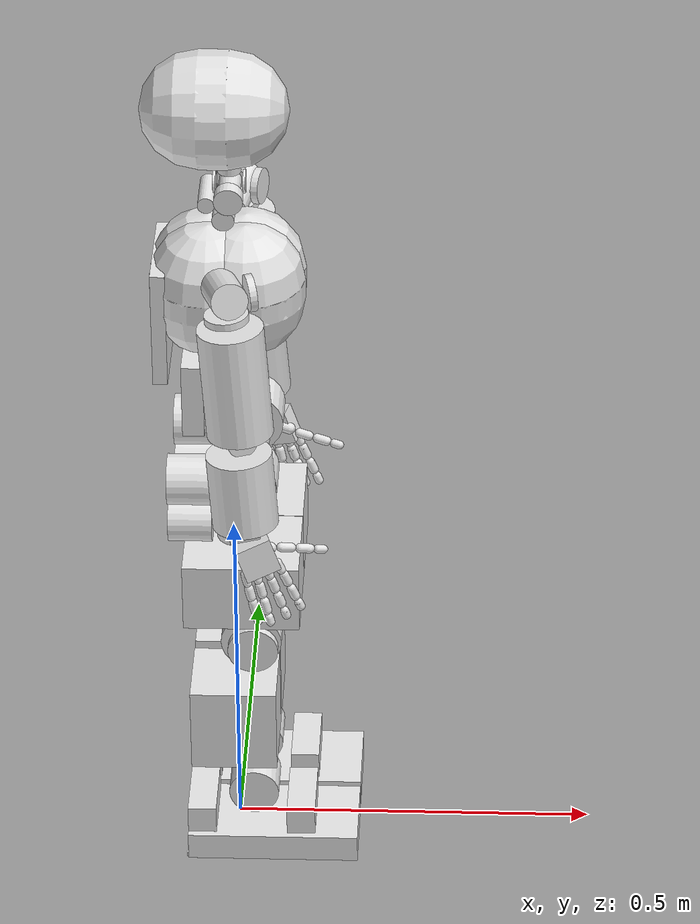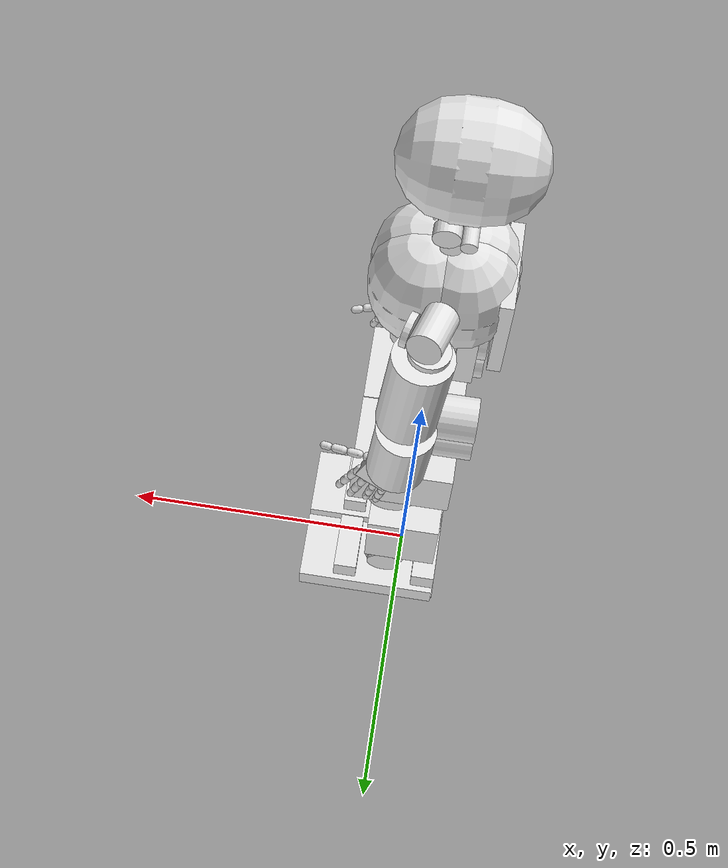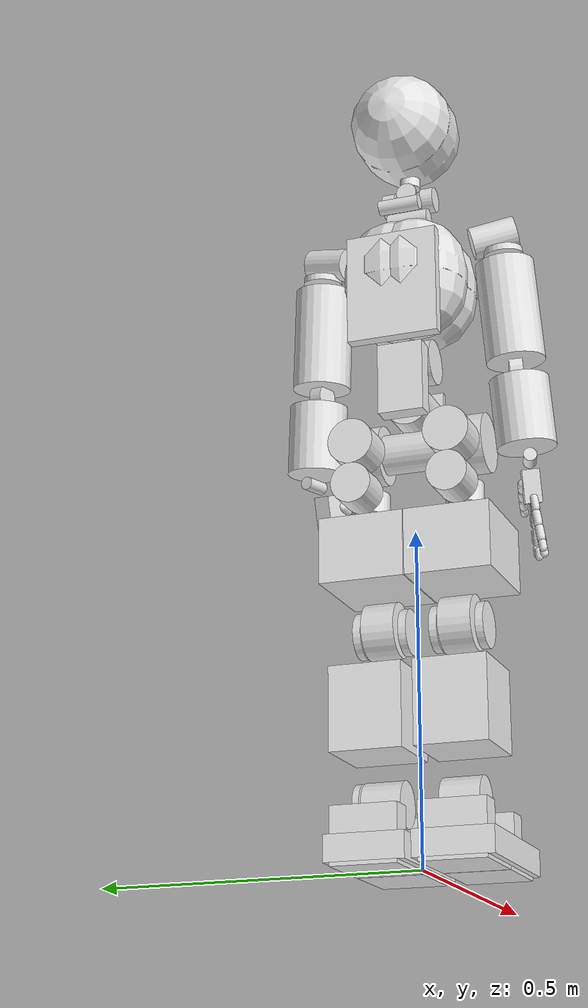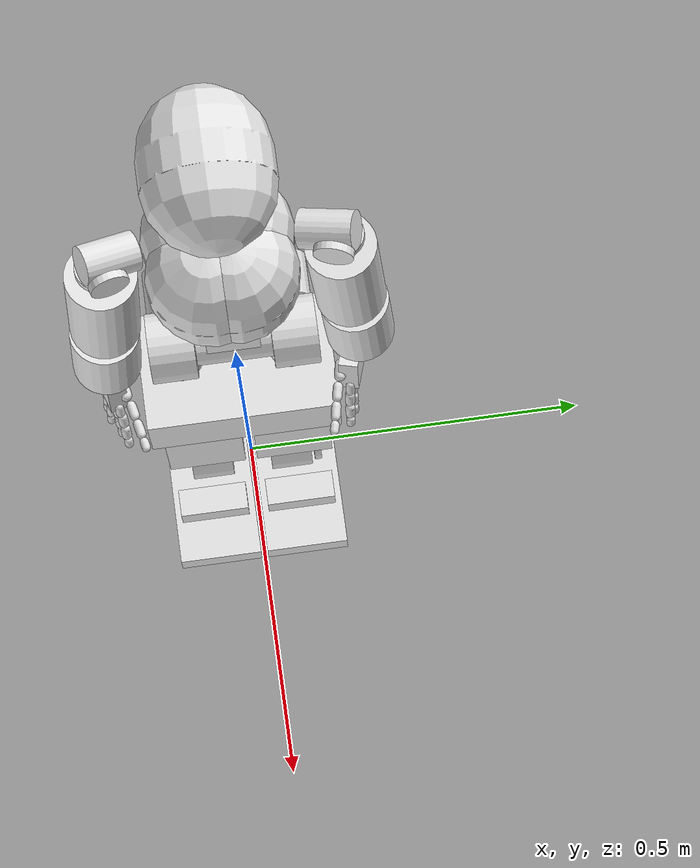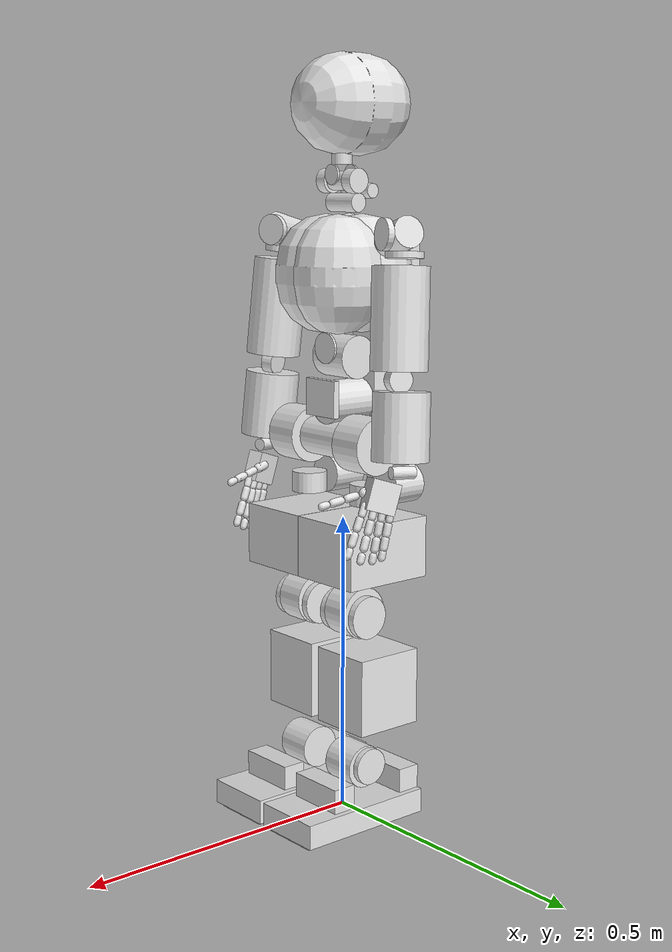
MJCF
<?xml version="1.0" ?>
<mujoco model="iCub">
	<compiler angle="radian" autolimits="true" balanceinertia="true" boundmass="0.001" boundinertia="0.000001"/>
	<default>
		<default class="iCub_visual">
			<geom contype="0" conaffinity="0"/>
		</default>
		<default class="iCub_collision">
			<geom rgba="0.9 0.9 0.9 1.0"/>
		</default>
	</default>
	<asset/>
	<worldbody>
		<body name="iCub" pos="0.0 0.0 0.0" quat="1.0 0.0 0.0 0.0">
			<freejoint/>
			<body name="base_footprint" pos="0.0 0.0 0.0" quat="1.0 0.0 0.0 0.0">
				<inertial mass="0.0" pos="0.0 0.0 0.0" quat="1.0 0.0 0.0 0.0" diaginertia="0.0 0.0 0.0"/>
				<body name="root_link" pos="0.0 0.0 0.6349999904632568" quat="1.0 0.0 0.0 0.0">
					<inertial mass="0.5866924524307251" pos="0.011262650601565838 0.0 0.02912449836730957" quat="0.7209774851799011 0.0 -0.6929585337638855 -0.0" diaginertia="0.0006618420011363924 0.0015093681868165731 0.0015251357108354568"/>
					<geom name="SM_root_link_collision_0" type="cylinder" pos="0.0020000000949949026 0.0 0.05999999865889549" quat="0.7071067690849304 0.0 0.7071067690849304 0.0" size="0.03500000014901161 0.03700000047683716 0.0" class="iCub_collision"/>
					<geom name="SM_root_link_collision_1" type="cylinder" pos="0.019999999552965164 0.0 0.0" quat="0.7071067690849304 0.7071067690849304 0.0 0.0" size="0.03099999949336052 0.05000000074505806 0.0" class="iCub_collision"/>
					<body name="r_hip_1" pos="0.02160000056028366 -0.040550000965595245 0.0" quat="1.0 0.0 0.0 0.0">
						<inertial mass="0.39885661005973816" pos="0.0 -0.03999999910593033 0.0" quat="-0.7071067690849304 0.0 0.0 0.7071067690849304" diaginertia="0.0004219902912154794 0.0009688226273283362 0.0009688226273283362"/>
						<geom name="SM_r_hip_1_collision_0" type="cylinder" pos="0.0 -0.03999999910593033 0.0" quat="0.7071067690849304 0.7071067690849304 0.0 0.0" size="0.04600000008940697 0.029999999329447746 0.0" class="iCub_collision"/>
						<joint name="r_hip_pitch" type="hinge" pos="0.0 0.0 0.0" range="-0.7853981852531433 2.0071287155151367" axis="0.0 -1.0 0.0"/>
						<body name="r_hip_2" pos="-0.04729999974370003 -0.03310000151395798 -0.008999999612569809" quat="1.0 0.0 0.0 0.0">
							<inertial mass="2.5818819999694824" pos="-0.0012447123881429434 0.0030985153280198574 -0.03421226143836975" quat="-0.508063793182373 0.45111268758773804 0.4899882972240448 0.5461501479148865" diaginertia="0.008091065101325512 0.01653752475976944 0.018502812832593918"/>
							<geom name="SM_r_hip_2_collision_0" type="cylinder" pos="-0.02800000086426735 0.0 0.0" quat="0.7071067690849304 0.0 -0.7071067690849304 0.0" size="0.03500000014901161 0.029999999329447746 0.0" class="iCub_collision"/>
							<geom name="SM_r_hip_2_collision_1" type="cylinder" pos="-0.02800000086426735 0.0 -0.06499999761581421" quat="0.7071067690849304 0.0 -0.7071067690849304 0.0" size="0.03099999949336052 0.029999999329447746 0.0" class="iCub_collision"/>
							<geom name="SM_r_hip_2_collision_2" type="cylinder" pos="0.03700000047683716 0.0 -0.0729999989271164" quat="1.0 0.0 0.0 0.0" size="0.028999999165534973 0.017000000923871994 0.0" class="iCub_collision"/>
							<joint name="r_hip_roll" type="hinge" pos="0.0 0.0 0.0" range="-0.1745329201221466 1.9547687768936157" axis="-1.0 0.0 0.0"/>
							<body name="r_hip_3" pos="0.03669999912381172 0.0 -0.08969999849796295" quat="1.0 0.0 0.0 0.0">
								<inertial mass="2.0799999237060547" pos="0.004999999888241291 0.00800000037997961 -0.07000000029802322" quat="-0.5035362839698792 0.44589680433273315 0.4866354763507843 0.5575062036514282" diaginertia="0.00733115104958415 0.015057817101478577 0.016565268859267235"/>
								<geom name="SM_r_hip_3_collision_0" type="box" pos="0.004999999888241291 0.00800000037997961 -0.07000000029802322" quat="1.0 0.0 0.0 0.0" size="0.07999999821186066 0.06499999761581421 0.05000000074505806" class="iCub_collision"/>
								<body name="r_upper_leg" pos="0.0 0.014999999664723873 -0.07090000063180923" quat="1.0 0.0 0.0 0.0">
									<inertial mass="0.09236282855272293" pos="0.017999999225139618 0.0 -0.10999999940395355" quat="1.0769857164726938e-16 0.6474995613098145 -2.7316121025959092e-17 0.7620658278465271" diaginertia="0.00014253893459681422 0.0012040879810228944 0.0012900546425953507"/>
									<geom name="SM_r_upper_leg_collision_0" type="cylinder" pos="0.017999999225139618 -0.03500000014901161 -0.10999999940395355" quat="0.7071067690849304 -0.7071067690849304 0.0 0.0" size="0.03500000014901161 0.006000000052154064 0.0" class="iCub_collision"/>
									<geom name="SM_r_upper_leg_collision_1" type="cylinder" pos="0.017999999225139618 0.03500000014901161 -0.10999999940395355" quat="0.7071067690849304 -0.7071067690849304 0.0 0.0" size="0.03500000014901161 0.006000000052154064 0.0" class="iCub_collision"/>
									<joint name="r_hip_yaw" type="hinge" pos="0.0 0.0 0.0" range="-1.3962633609771729 1.3962633609771729" axis="0.0 0.0 -1.0"/>
									<body name="r_lower_leg" pos="0.014999999664723873 -0.024900000542402267 -0.10620000213384628" quat="1.0 0.0 0.0 0.0">
										<inertial mass="2.1711955070495605" pos="-0.019150739535689354 0.02116985246539116 -0.12723489105701447" quat="-0.3837120831012726 -0.5399561524391174 -0.5103661417961121 0.5483965873718262" diaginertia="0.004571052268147469 0.04954816401004791 0.0501323938369751"/>
										<geom name="SM_r_lower_leg_collision_0" type="cylinder" pos="0.0 0.02500000037252903 0.0" quat="0.7071067690849304 -0.7071067690849304 0.0 0.0" size="0.041999999433755875 0.02500000037252903 0.0" class="iCub_collision"/>
										<geom name="SM_r_lower_leg_collision_1" type="box" pos="-0.02500000037252903 0.019999999552965164 -0.12999999523162842" quat="1.0 0.0 0.0 0.0" size="0.05999999865889549 0.054999999701976776 0.06300000101327896" class="iCub_collision"/>
										<geom name="SM_r_lower_leg_collision_2" type="cylinder" pos="0.0 0.02500000037252903 -0.25999999046325684" quat="0.7071067690849304 -0.7071067690849304 0.0 0.0" size="0.03500000014901161 0.029999999329447746 0.0" class="iCub_collision"/>
										<joint name="r_knee" type="hinge" pos="0.0 0.0 0.0" range="-1.2217304706573486 0.0872664600610733" axis="0.0 -1.0 0.0"/>
										<body name="r_ankle_1" pos="0.0 0.0005000000237487257 -0.2559889853000641" quat="1.0 0.0 0.0 0.0">
											<inertial mass="0.028274331241846085" pos="0.0 0.014999999664723873 0.0" quat="-0.7071067690849304 3.0616802089477105e-15 3.0616802089477105e-15 0.7071067690849304" diaginertia="1.2723448890028521e-05 1.2959068044438027e-05 1.2959068044438027e-05"/>
											<geom name="SM_r_ankle_1_collision_0" type="cylinder" pos="0.0 0.014999999664723873 0.0" quat="0.7071067690849304 -0.7071067690849304 0.0 0.0" size="0.029999999329447746 0.004999999888241291 0.0" class="iCub_collision"/>
											<joint name="r_ankle_pitch" type="hinge" pos="0.0 0.0 0.0" range="-0.7853981852531433 0.7853981852531433" axis="0.0 1.0 0.0"/>
											<body name="r_ankle_2" pos="-0.05274999886751175 0.018200000748038292 -0.03500000014901161" quat="1.0 0.0 0.0 0.0">
												<inertial mass="1.612399935722351" pos="0.06708012521266937 0.0 -0.026717934757471085" quat="0.9921354055404663 -2.4898277257073614e-15 0.12516944110393524 3.422103104158019e-16" diaginertia="0.002862008521333337 0.01751437783241272 0.01818450167775154"/>
												<geom name="SM_r_ankle_2_collision_0" type="box" pos="0.11999999731779099 0.0 0.0" quat="1.0 0.0 0.0 0.0" size="0.019999999552965164 0.05000000074505806 0.019999999552965164" class="iCub_collision"/>
												<geom name="SM_r_ankle_2_collision_1" type="box" pos="-0.019999999552965164 0.0 0.0" quat="1.0 0.0 0.0 0.0" size="0.019999999552965164 0.05000000074505806 0.019999999552965164" class="iCub_collision"/>
												<geom name="SM_r_ankle_2_collision_2" type="box" pos="0.07999999821186066 0.0 -0.03999999910593033" quat="1.0 0.0 0.0 0.0" size="0.11999999731779099 0.05999999865889549 0.019999999552965164" class="iCub_collision"/>
												<joint name="r_ankle_roll" type="hinge" pos="0.0 0.0 0.0" range="-0.4363323152065277 0.4363323152065277" axis="-1.0 0.0 0.0"/>
												<body name="r_foot_rear" pos="0.01600000075995922 0.0 -0.0658000037074089" quat="1.0 0.0 0.0 0.0">
													<inertial mass="0.07020000368356705" pos="0.0 0.0 0.003000000026077032" quat="1.0 0.0 0.0 0.0" diaginertia="5.934240107308142e-05 8.092304778983817e-05 0.00013858065358363092"/>
													<geom name="SM_r_foot_rear_collision_0" type="box" pos="0.0 0.0 0.003000000026077032" quat="1.0 0.0 0.0 0.0" size="0.05849999934434891 0.05000000074505806 0.003000000026077032" class="iCub_collision"/>
													<body name="r_sole" pos="0.05962999910116196 0.0 0.0" quat="1.0 0.0 0.0 0.0">
														<inertial mass="0.0" pos="0.0 0.0 0.0" quat="1.0 0.0 0.0 0.0" diaginertia="0.0 0.0 0.0"/>
													</body>
												</body>
												<body name="r_foot_front" pos="0.1352500021457672 0.0 -0.0658000037074089" quat="1.0 0.0 0.0 0.0">
													<inertial mass="0.07020000368356705" pos="0.0 0.0 0.003000000026077032" quat="1.0 0.0 0.0 0.0" diaginertia="5.934240107308142e-05 8.092304778983817e-05 0.00013858065358363092"/>
													<geom name="SM_r_foot_front_collision_0" type="box" pos="0.0 0.0 0.003000000026077032" quat="1.0 0.0 0.0 0.0" size="0.05849999934434891 0.05000000074505806 0.003000000026077032" class="iCub_collision"/>
												</body>
											</body>
										</body>
									</body>
								</body>
							</body>
						</body>
					</body>
					<body name="torso_1" pos="0.0 0.0 0.060499999672174454" quat="1.0 0.0 0.0 0.0">
						<inertial mass="0.5539368987083435" pos="-0.01743880845606327 0.0 0.05013999715447426" quat="0.5562618970870972 0.5562618970870972 0.43654632568359375 -0.43654632568359375" diaginertia="0.000921399740036577 0.002356593729928136 0.0028055247385054827"/>
						<geom name="SM_torso_1_collision_0" type="cylinder" pos="0.0 0.0 0.0729999989271164" quat="0.7071067690849304 -0.7071067690849304 0.0 0.0" size="0.03500000014901161 0.0364999994635582 0.0" class="iCub_collision"/>
						<geom name="SM_torso_1_collision_1" type="box" pos="-0.05000000074505806 0.0 0.029999999329447746" quat="1.0 0.0 0.0 0.0" size="0.014999999664723873 0.03500000014901161 0.054999999701976776" class="iCub_collision"/>
						<geom name="SM_torso_1_collision_2" type="box" pos="0.04500000178813934 0.0 0.00800000037997961" quat="1.0 0.0 0.0 0.0" size="0.004999999888241291 0.03500000014901161 0.029999999329447746" class="iCub_collision"/>
						<joint name="torso_roll" type="hinge" pos="0.0 0.0 0.0" range="-0.40142571926116943 0.40142571926116943" axis="-1.0 0.0 0.0"/>
						<body name="torso_2" pos="0.0 0.0 0.07249999791383743" quat="1.0 0.0 0.0 0.0">
							<inertial mass="0.007853982038795948" pos="0.03799999877810478 0.0 0.014999999664723873" quat="0.979069709777832 -8.504677982043145e-17 -0.203525111079216 1.41744627519515e-17" diaginertia="2.2762287699151784e-06 1.4345951967698056e-05 1.4524092875944916e-05"/>
							<geom name="SM_torso_2_collision_0" type="cylinder" pos="0.03799999877810478 0.0 0.014999999664723873" quat="0.7071067690849304 0.0 -0.7071067690849304 0.0" size="0.02500000037252903 0.0020000000949949026 0.0" class="iCub_collision"/>
							<joint name="torso_pitch" type="hinge" pos="0.0 0.0 0.0" range="-0.3141592741012573 0.7853981852531433" axis="0.0 1.0 0.0"/>
							<body name="chest" pos="0.0 0.0 0.06447000056505203" quat="1.0 0.0 0.0 0.0">
								<inertial mass="3.0083560943603516" pos="-0.014636729843914509 0.0005911639309488237 0.07015182077884674" quat="0.5684014558792114 0.5683584213256836 0.4202249348163605 -0.42106953263282776" diaginertia="0.014126136898994446 0.018721861764788628 0.0223391093313694"/>
								<geom name="SM_chest_collision_0" type="capsule" pos="-0.02500000037252903 0.014999999664723873 0.06800000369548798" quat="1.0 0.0 0.0 0.0" size="0.07999999821186066 0.014999999664723873 0.0" class="iCub_collision"/>
								<geom name="SM_chest_collision_1" type="capsule" pos="-0.02500000037252903 -0.014999999664723873 0.06800000369548798" quat="1.0 0.0 0.0 0.0" size="0.07999999821186066 0.014999999664723873 0.0" class="iCub_collision"/>
								<geom name="SM_chest_collision_2" type="capsule" pos="0.02500000037252903 0.014999999664723873 0.06800000369548798" quat="1.0 0.0 0.0 0.0" size="0.07999999821186066 0.014999999664723873 0.0" class="iCub_collision"/>
								<geom name="SM_chest_collision_3" type="capsule" pos="0.02500000037252903 -0.014999999664723873 0.06800000369548798" quat="1.0 0.0 0.0 0.0" size="0.07999999821186066 0.014999999664723873 0.0" class="iCub_collision"/>
								<geom name="SM_chest_collision_4" type="box" pos="-0.09000000357627869 0.0 0.029999999329447746" quat="1.0 0.0 0.0 0.0" size="0.009999999776482582 0.07000000029802322 0.08500000089406967" class="iCub_collision"/>
								<joint name="torso_yaw" type="hinge" pos="0.0 0.0 -1.3877787807814457e-17" range="-0.7504915595054626 0.7504915595054626" axis="0.0 0.0 -1.0"/>
								<body name="chest_depth_frame" pos="0.08941149711608887 0.017500000074505806 0.09929949790239334" quat="0.5 -0.5 0.5 -0.5">
									<inertial mass="0.0" pos="0.0 0.0 0.0" quat="1.0 0.0 0.0 0.0" diaginertia="0.0 0.0 0.0"/>
								</body>
								<body name="r_shoulder_1" pos="-0.02083509974181652 -0.03974229842424393 0.10520289838314056" quat="0.9835063815116882 -0.12521222233772278 -0.01648440770804882 0.129481241106987">
									<inertial mass="0.13744468986988068" pos="0.0 -0.10000000149011612 0.0" quat="-0.7071067690849304 0.0 0.0 0.7071067690849304" diaginertia="4.2951465729856864e-05 0.0014520458644255996 0.0014520458644255996"/>
									<geom name="SM_r_shoulder_1_collision_0" type="cylinder" pos="0.0 -0.10000000149011612 0.0" quat="0.7071067690849304 -0.7071067690849304 0.0 0.0" size="0.02500000037252903 0.03500000014901161 0.0" class="iCub_collision"/>
									<joint name="r_shoulder_pitch" type="hinge" pos="0.0 0.0 1.3877787807814457e-17" range="-0.3490658402442932 3.054326295852661" axis="1.4990443730766856e-07 -1.0 -1.456618718975733e-07"/>
									<body name="r_shoulder_2" pos="0.007489008363336325 -0.11150041222572327 0.00040278589585796" quat="0.99583500623703 0.08712433278560638 -0.026768436655402184 0.0023416290059685707">
										<inertial mass="0.04790928587317467" pos="0.0043442631140351295 0.0 -0.0177049171179533" quat="0.3341016173362732 -0.3341016173362732 0.6231982707977295 0.6231982707977295" diaginertia="2.5417031793040223e-05 4.381744656711817e-05 5.037510709371418e-05"/>
										<geom name="SM_r_shoulder_2_collision_0" type="cylinder" pos="-0.009999999776482582 0.0 -0.029999999329447746" quat="1.0 0.0 0.0 0.0" size="0.029999999329447746 0.004999999888241291 0.0" class="iCub_collision"/>
										<geom name="SM_r_shoulder_2_collision_1" type="cylinder" pos="0.02500000037252903 0.0 0.0" quat="0.7071067690849304 0.0 -0.7071067690849304 0.0" size="0.02500000037252903 0.004999999888241291 0.0" class="iCub_collision"/>
										<joint name="r_shoulder_roll" type="hinge" pos="7.424289277617633e-18 3.63239557692615e-17 2.3736409243990934e-17" range="0.20943951606750488 2.8448867797851562" axis="-1.0 4.2105021691440925e-08 1.983887045753363e-07"/>
										<body name="r_shoulder_3" pos="-0.006849946454167366 2.190499657217515e-07 -0.0542999804019928" quat="1.0 0.0 3.469446951953614e-18 -1.1926223897340549e-17">
											<inertial mass="0.0" pos="0.0 0.0 0.0" quat="1.0 0.0 0.0 0.0" diaginertia="0.0 0.0 0.0"/>
											<body name="r_upper_arm" pos="-3.469446951953614e-18 4.2183273762930185e-07 -0.022499941289424896" quat="1.0 0.0 3.469446951953614e-18 -1.1926223897340549e-17">
												<inertial mass="1.0178760290145874" pos="0.0 0.0 -0.05000000074505806" quat="0.7071067690849304 0.0 0.7071067690849304 0.0" diaginertia="0.0010305995820090175 0.005231459159404039 0.005231459159404039"/>
												<geom name="SM_r_upper_arm_collision_0" type="cylinder" pos="0.0 0.0 -0.05000000074505806" quat="1.0 0.0 0.0 0.0" size="0.04500000178813934 0.07999999821186066 0.0" class="iCub_collision"/>
												<joint name="r_shoulder_yaw" type="hinge" pos="2.4537583298085294e-17 4.3083827936277555e-17 1.2062363267787996e-16" range="-0.8726646304130554 1.3962633609771729" axis="-3.7876212388709973e-08 2.805197318878072e-08 1.0"/>
												<body name="r_elbow_1" pos="0.009999931789934635 0.001499640173278749 -0.1237003356218338" quat="1.0 0.0 3.469446951953614e-18 -1.1926223897340549e-17">
													<inertial mass="0.025132739916443825" pos="-0.009999999776482582 0.0 -0.019999999552965164" quat="0.601500928401947 -0.601500928401947 -0.37174803018569946 -0.37174803018569946" diaginertia="3.3510318644403014e-06 1.591740146977827e-05 1.7592916265130043e-05"/>
													<geom name="SM_r_elbow_1_collision_0" type="cylinder" pos="-0.009999999776482582 0.0 -0.019999999552965164" quat="0.7071067690849304 -0.7071067690849304 0.0 0.0" size="0.019999999552965164 0.009999999776482582 0.0" class="iCub_collision"/>
													<joint name="r_elbow" type="hinge" pos="1.5342827243041825e-17 4.8768461259925727e-17 7.276389549529274e-17" range="-0.05235987901687622 1.3089969158172607" axis="2.494957698218059e-07 -1.0 -2.454089553793892e-07"/>
													<body name="r_forearm" pos="-0.014999869279563427 -0.001999649917706847 -0.055300064384937286" quat="1.0 0.0 3.469446951953614e-18 -1.1926223897340549e-17">
														<inertial mass="0.687066376209259" pos="0.0 0.0 -0.035999998450279236" quat="0.7071067690849304 0.0 0.7071067690849304 0.0" diaginertia="0.0006956547731533647 0.0019060939084738493 0.0019060939084738493"/>
														<geom name="SM_r_forearm_collision_0" type="cylinder" pos="0.0 0.0 -0.035999998450279236" quat="1.0 0.0 0.0 0.0" size="0.04500000178813934 0.05400000140070915 0.0" class="iCub_collision"/>
														<joint name="r_wrist_prosup" type="hinge" pos="2.042410841044892e-17 1.9499661284027006e-17 5.623888488184728e-17" range="-1.535889744758606 1.535889744758606" axis="-3.7876212388709973e-08 2.805197318878072e-08 1.0"/>
														<body name="r_wrist_1" pos="0.016299953684210777 -0.002007442992180586 -0.10750007629394531" quat="1.0 0.0 3.469446951953614e-18 -1.1926223897340549e-17">
															<inertial mass="0.012566369958221912" pos="-0.019999999552965164 0.0 0.0" quat="0.0 1.0 0.0 -3.549073673823684e-17" diaginertia="6.283184461608471e-07 7.01622275300906e-06 7.01622275300906e-06"/>
															<geom name="SM_r_wrist_1_collision_0" type="cylinder" pos="-0.019999999552965164 0.0 0.0" quat="0.7071067690849304 0.0 -0.7071067690849304 0.0" size="0.009999999776482582 0.019999999552965164 0.0" class="iCub_collision"/>
															<joint name="r_wrist_pitch" type="hinge" pos="9.872227730072362e-18 3.1374236023919743e-17 -8.167046017056151e-17" range="-1.2217304706573486 0.4363323152065277" axis="1.0 4.2105021691440925e-08 -1.983887045753363e-07"/>
															<body name="r_hand" pos="-0.016300123184919357 0.006999390199780464 0.0" quat="-7.312061383896867e-14 0.7071067690849304 7.311908240340004e-14 0.7071067690849304">
																<inertial mass="0.0650000050663948" pos="-0.03999999910593033 0.004999999888241291 0.009999999776482582" quat="0.9907810688018799 0.042749423533678055 0.11008170247077942 -0.06638852506875992" diaginertia="1.764310036378447e-05 0.00012932834215462208 0.00013876857701689005"/>
																<geom name="SM_r_hand_collision_0" type="box" pos="-0.03999999910593033 0.004999999888241291 0.009999999776482582" quat="-0.7010573744773865 0.7010573744773865 -0.09229592978954315 -0.09229592978954315" size="0.02500000037252903 0.02500000037252903 0.013000000268220901" class="iCub_collision"/>
																<joint name="r_wrist_yaw" type="hinge" pos="-7.534170295827952e-18 -2.6658087268144582e-17 -1.7189102642066309e-18" range="-0.2617993950843811 0.6108652353286743" axis="-2.494957698218059e-07 1.0 2.454089553793892e-07"/>
																<body name="r_hand_little_0" pos="-0.06362900137901306 0.004443199839442968 -0.010110927745699883" quat="0.08513370156288147 0.02448935993015766 -0.6986569166183472 0.7099514007568359">
																	<inertial mass="0.0015833628131076694" pos="0.007000000216066837 -0.0020000000949949026 -0.0010000000474974513" quat="0.964142382144928 0.22760315239429474 0.031356215476989746 -0.1328270584344864" diaginertia="2.9456517225412426e-08 1.246574612423501e-07 1.2561345386075118e-07"/>
																	<geom name="SM_r_hand_little_0_collision_0" type="capsule" pos="0.007000000216066837 -0.0020000000949949026 -0.0010000000474974513" quat="-7.312061383896867e-14 0.7071067690849304 7.311908240340004e-14 0.7071067690849304" size="0.006000000052154064 0.007000000216066837 0.0" class="iCub_collision"/>
																	<joint name="r_hand_little_0_joint" type="hinge" pos="2.993997391133394e-18 1.906093461329623e-17 -1.9513725008801632e-17" range="0.0 0.3490658402442932" axis="0.0 0.0 1.0"/>
																	<body name="r_hand_little_1" pos="0.014800000004470348 -0.0017500000540167093 0.0" quat="0.7071067690849304 0.7071067690849304 -1.962615539765984e-17 -1.962615539765984e-17">
																		<inertial mass="0.0018582522170618176" pos="0.014999999664723873 0.0 0.0" quat="-2.5858776620359732e-15 2.7813018772726887e-28 1.0755736850210501e-13 1.0" diaginertia="3.925557834350002e-08 4.6808597176095645e-07 4.6808597176095645e-07"/>
																		<geom name="SM_r_hand_little_1_collision_0" type="capsule" pos="0.014999999664723873 0.0 0.0" quat="-7.312061383896867e-14 0.7071067690849304 7.311908240340004e-14 0.7071067690849304" size="0.006500000134110451 0.007000000216066837 0.0" class="iCub_collision"/>
																		<joint name="r_hand_little_1_joint" type="hinge" pos="3.010923863930975e-17 -1.281928249736628e-16 -1.6691014181856278e-17" range="0.0 1.5707963705062866" axis="0.0 0.0 1.0"/>
																		<body name="r_hand_little_2" pos="0.021900000050663948 -5.551115123125783e-17 0.0" quat="1.0 1.5612511283791264e-17 -6.938893903907228e-18 3.0814879110195774e-33">
																			<inertial mass="0.0018582522170618176" pos="0.014999999664723873 0.0 0.0" quat="-2.5858776620359732e-15 2.7813018772726887e-28 1.0755736850210501e-13 1.0" diaginertia="3.925557834350002e-08 4.6808597176095645e-07 4.6808597176095645e-07"/>
																			<geom name="SM_r_hand_little_2_collision_0" type="capsule" pos="0.014999999664723873 0.0 0.0" quat="-7.312061383896867e-14 0.7071067690849304 7.311908240340004e-14 0.7071067690849304" size="0.006500000134110451 0.007000000216066837 0.0" class="iCub_collision"/>
																			<joint name="r_hand_little_2_joint" type="hinge" pos="1.6818806193568996e-19 4.737618394010097e-17 3.7772650115584823e-17" range="0.0 1.5707963705062866" axis="0.0 0.0 1.0"/>
																			<body name="r_hand_little_3" pos="0.01899999938905239 5.551115123125783e-17 -1.3877787807814457e-17" quat="1.0 1.5612511283791264e-17 -6.938893903907228e-18 3.0814879110195774e-33">
																				<inertial mass="0.0009047787170857191" pos="0.014999999664723873 0.0 0.0" quat="1.713069078680251e-15 1.9525727777554028e-28 -1.1398098177101135e-13 1.0" diaginertia="1.628601786762829e-08 2.1654371096246905e-07 2.1654371096246905e-07"/>
																				<geom name="SM_r_hand_little_3_collision_0" type="capsule" pos="0.014999999664723873 0.0 0.0" quat="-7.312061383896867e-14 0.7071067690849304 7.311908240340004e-14 0.7071067690849304" size="0.006000000052154064 0.004000000189989805 0.0" class="iCub_collision"/>
																				<joint name="r_hand_little_3_joint" type="hinge" pos="-1.1888044548987551e-17 -5.1267241541550415e-17 -2.837872054956716e-17" range="0.0 1.5707963705062866" axis="0.0 0.0 1.0"/>
																				<body name="r_hand_little_tip" pos="0.01679999940097332 0.0 -2.7755575615628914e-17" quat="0.7071067690849304 -0.7071067690849304 -7.237144792547308e-17 7.237144792547308e-17">
																					<inertial mass="0.0" pos="0.0 0.0 0.0" quat="1.0 0.0 0.0 0.0" diaginertia="0.0 0.0 0.0"/>
																				</body>
																			</body>
																		</body>
																	</body>
																</body>
																<body name="r_gripper_tool_frame" pos="1.1102230246251565e-16 2.7755575615628914e-17 0.12999999523162842" quat="1.0 1.1275702593849246e-17 0.0 0.0">
																	<inertial mass="0.0" pos="0.0 0.0 0.0" quat="1.0 0.0 0.0 0.0" diaginertia="0.0 0.0 0.0"/>
																</body>
																<body name="r_hand_middle_0" pos="-0.05754045024514198 0.0060431999154388905 0.023777974769473076" quat="0.09229592978954315 0.09229592978954315 -0.7010573744773865 0.7010573744773865">
																	<inertial mass="0.0015833628131076694" pos="0.007000000216066837 0.0020000000949949026 -0.0010000000474974513" quat="0.964142382144928 -0.22760315239429474 0.031356215476989746 0.1328270584344864" diaginertia="2.9456517225412426e-08 1.246574612423501e-07 1.2561345386075118e-07"/>
																	<geom name="SM_r_hand_middle_0_collision_0" type="capsule" pos="0.007000000216066837 0.0020000000949949026 -0.0010000000474974513" quat="-7.312061383896867e-14 0.7071067690849304 7.311908240340004e-14 0.7071067690849304" size="0.006000000052154064 0.007000000216066837 0.0" class="iCub_collision"/>
																	<joint name="r_hand_middle_0_joint" type="hinge" pos="3.9026827977782624e-18 -2.835248238053698e-17 -1.6511623522411903e-16" range="0.0 0.3490658503988659" axis="0.0 0.0 1.0"/>
																	<body name="r_hand_middle_1" pos="0.015300000086426735 0.002199999988079071 0.0" quat="0.7071067690849304 0.7071067690849304 -1.4719616134654573e-17 5.887846453861829e-17">
																		<inertial mass="0.0018582522170618176" pos="0.014999999664723873 0.0 0.0" quat="-2.5858776620359732e-15 2.7813018772726887e-28 1.0755736850210501e-13 1.0" diaginertia="3.925557834350002e-08 4.6808597176095645e-07 4.6808597176095645e-07"/>
																		<geom name="SM_r_hand_middle_1_collision_0" type="capsule" pos="0.014999999664723873 0.0 0.0" quat="-7.312061383896867e-14 0.7071067690849304 7.311908240340004e-14 0.7071067690849304" size="0.006500000134110451 0.007000000216066837 0.0" class="iCub_collision"/>
																		<joint name="r_hand_middle_1_joint" type="hinge" pos="6.1125851397198316e-18 -1.5268602672316217e-17 -1.2165533038816428e-17" range="0.0 1.5707963705062866" axis="0.0 0.0 1.0"/>
																		<body name="r_hand_middle_2" pos="0.025800000876188278 2.7755575615628914e-17 0.0" quat="1.0 1.5612511283791264e-17 1.3877787807814457e-17 -3.469446951953614e-18">
																			<inertial mass="0.0018582522170618176" pos="0.014999999664723873 0.0 0.0" quat="-2.5858776620359732e-15 2.7813018772726887e-28 1.0755736850210501e-13 1.0" diaginertia="3.925557834350002e-08 4.6808597176095645e-07 4.6808597176095645e-07"/>
																			<geom name="SM_r_hand_middle_2_collision_0" type="capsule" pos="0.014999999664723873 0.0 0.0" quat="-7.312061383896867e-14 0.7071067690849304 7.311908240340004e-14 0.7071067690849304" size="0.006500000134110451 0.007000000216066837 0.0" class="iCub_collision"/>
																			<joint name="r_hand_middle_2_joint" type="hinge" pos="-1.4617530466536954e-17 -1.4615110136064624e-17 -4.875819760288517e-17" range="0.0 1.5707963705062866" axis="0.0 0.0 1.0"/>
																			<body name="r_hand_middle_3" pos="0.024000000208616257 2.7755575615628914e-17 2.7755575615628914e-17" quat="1.0 1.5612511283791264e-17 1.3877787807814457e-17 -3.469446951953614e-18">
																				<inertial mass="0.0009047787170857191" pos="0.014999999664723873 0.0 0.0" quat="1.713069078680251e-15 1.9525727777554028e-28 -1.1398098177101135e-13 1.0" diaginertia="1.628601786762829e-08 2.1654371096246905e-07 2.1654371096246905e-07"/>
																				<geom name="SM_r_hand_middle_3_collision_0" type="capsule" pos="0.014999999664723873 0.0 0.0" quat="-7.312061383896867e-14 0.7071067690849304 7.311908240340004e-14 0.7071067690849304" size="0.006000000052154064 0.004000000189989805 0.0" class="iCub_collision"/>
																				<joint name="r_hand_middle_3_joint" type="hinge" pos="3.704806636876797e-17 -3.373227648740221e-17 1.5297853433137317e-17" range="0.0 1.5707963705062866" axis="0.0 0.0 1.0"/>
																				<body name="r_hand_middle_tip" pos="0.01679999940097332 0.0 0.0" quat="0.7071067690849304 -0.7071067690849304 5.289862368923975e-17 -2.0699461947116796e-17">
																					<inertial mass="0.0" pos="0.0 0.0 0.0" quat="1.0 0.0 0.0 0.0" diaginertia="0.0 0.0 0.0"/>
																				</body>
																			</body>
																		</body>
																	</body>
																</body>
																<body name="r_hand_index_0" pos="-0.05255843326449394 0.005143200047314167 0.039473339915275574" quat="-0.12013258039951324 -0.11427371948957443 0.7273476123809814 -0.6659393310546875">
																	<inertial mass="0.0015833628131076694" pos="0.007000000216066837 0.0020000000949949026 -0.0010000000474974513" quat="0.964142382144928 -0.22760315239429474 0.031356215476989746 0.1328270584344864" diaginertia="2.9456517225412426e-08 1.246574612423501e-07 1.2561345386075118e-07"/>
																	<geom name="SM_r_hand_index_0_collision_0" type="capsule" pos="0.007000000216066837 0.0020000000949949026 -0.0010000000474974513" quat="-7.312061383896867e-14 0.7071067690849304 7.311908240340004e-14 0.7071067690849304" size="0.006000000052154064 0.007000000216066837 0.0" class="iCub_collision"/>
																	<joint name="r_hand_index_0_joint" type="hinge" pos="1.2200603842427451e-17 -4.0746169203088395e-17 -3.8314294598129446e-17" range="-0.3490658402442932 0.0" axis="0.0 0.0 1.0"/>
																	<body name="r_hand_index_1" pos="0.014800000004470348 0.0017500000540167093 0.0" quat="0.7071067690849304 0.7071067690849304 3.189250438235362e-17 -4.17055795996417e-17">
																		<inertial mass="0.0018582522170618176" pos="0.014999999664723873 0.0 0.0" quat="-2.5858776620359732e-15 2.7813018772726887e-28 1.0755736850210501e-13 1.0" diaginertia="3.925557834350002e-08 4.6808597176095645e-07 4.6808597176095645e-07"/>
																		<geom name="SM_r_hand_index_1_collision_0" type="capsule" pos="0.014999999664723873 0.0 0.0" quat="-7.312061383896867e-14 0.7071067690849304 7.311908240340004e-14 0.7071067690849304" size="0.006500000134110451 0.007000000216066837 0.0" class="iCub_collision"/>
																		<joint name="r_hand_index_1_joint" type="hinge" pos="-1.3139740869347693e-17 3.035666490413661e-17 1.057552729254761e-17" range="0.0 1.5707963705062866" axis="0.0 0.0 1.0"/>
																		<body name="r_hand_index_2" pos="0.02590000070631504 2.7755575615628914e-17 0.0" quat="1.0 1.0408340855860843e-17 1.3877787807814457e-17 3.469446951953614e-18">
																			<inertial mass="0.0018582522170618176" pos="0.014999999664723873 0.0 0.0" quat="-2.5858776620359732e-15 2.7813018772726887e-28 1.0755736850210501e-13 1.0" diaginertia="3.925557834350002e-08 4.6808597176095645e-07 4.6808597176095645e-07"/>
																			<geom name="SM_r_hand_index_2_collision_0" type="capsule" pos="0.014999999664723873 0.0 0.0" quat="-7.312061383896867e-14 0.7071067690849304 7.311908240340004e-14 0.7071067690849304" size="0.006500000134110451 0.007000000216066837 0.0" class="iCub_collision"/>
																			<joint name="r_hand_index_2_joint" type="hinge" pos="2.799935566831564e-17 -5.223902656006751e-17 5.552864775557455e-17" range="0.0 1.5707963705062866" axis="0.0 0.0 1.0"/>
																			<body name="r_hand_index_3" pos="0.02199999988079071 2.7755575615628914e-17 0.0" quat="1.0 1.0408340855860843e-17 1.3877787807814457e-17 3.469446951953614e-18">
																				<inertial mass="0.0009047787170857191" pos="0.014999999664723873 0.0 0.0" quat="1.713069078680251e-15 1.9525727777554028e-28 -1.1398098177101135e-13 1.0" diaginertia="1.628601786762829e-08 2.1654371096246905e-07 2.1654371096246905e-07"/>
																				<geom name="SM_r_hand_index_3_collision_0" type="capsule" pos="0.014999999664723873 0.0 0.0" quat="-7.312061383896867e-14 0.7071067690849304 7.311908240340004e-14 0.7071067690849304" size="0.006000000052154064 0.004000000189989805 0.0" class="iCub_collision"/>
																				<joint name="r_hand_index_3_joint" type="hinge" pos="-8.915341061567957e-18 -1.8695755879549995e-17 -2.7833284271094595e-17" range="0.0 1.5707963705062866" axis="0.0 0.0 1.0"/>
																				<body name="r_hand_index_tip" pos="0.01679999940097332 -2.7755575615628914e-17 0.0" quat="0.7071067690849304 -0.7071067690849304 -6.869154637335128e-17 -4.906538932133021e-17">
																					<inertial mass="0.0" pos="0.0 0.0 0.0" quat="1.0 0.0 0.0 0.0" diaginertia="0.0 0.0 0.0"/>
																				</body>
																			</body>
																		</body>
																	</body>
																</body>
																<body name="r_hand_ring_0" pos="-0.06069108471274376 0.0054432000033557415 0.008658226579427719" quat="0.08513370156288147 0.02448935993015766 -0.6986569166183472 0.7099514007568359">
																	<inertial mass="0.0015833628131076694" pos="0.007000000216066837 0.0020000000949949026 -0.0010000000474974513" quat="0.964142382144928 -0.22760315239429474 0.031356215476989746 0.1328270584344864" diaginertia="2.9456517225412426e-08 1.246574612423501e-07 1.2561345386075118e-07"/>
																	<geom name="SM_r_hand_ring_0_collision_0" type="capsule" pos="0.007000000216066837 0.0020000000949949026 -0.0010000000474974513" quat="-7.312061383896867e-14 0.7071067690849304 7.311908240340004e-14 0.7071067690849304" size="0.006000000052154064 0.007000000216066837 0.0" class="iCub_collision"/>
																	<joint name="r_hand_ring_0_joint" type="hinge" pos="7.389780129642533e-18 -4.246371710082615e-17 -1.1039573630956389e-16" range="0.0 0.3490658402442932" axis="0.0 0.0 1.0"/>
																	<body name="r_hand_ring_1" pos="0.014800000004470348 0.0017500000540167093 0.0" quat="0.7071067690849304 0.7071067690849304 -1.962615539765984e-17 -1.962615539765984e-17">
																		<inertial mass="0.0018582522170618176" pos="0.014999999664723873 0.0 0.0" quat="-2.5858776620359732e-15 2.7813018772726887e-28 1.0755736850210501e-13 1.0" diaginertia="3.925557834350002e-08 4.6808597176095645e-07 4.6808597176095645e-07"/>
																		<geom name="SM_r_hand_ring_1_collision_0" type="capsule" pos="0.014999999664723873 0.0 0.0" quat="-7.312061383896867e-14 0.7071067690849304 7.311908240340004e-14 0.7071067690849304" size="0.006500000134110451 0.007000000216066837 0.0" class="iCub_collision"/>
																		<joint name="r_hand_ring_1_joint" type="hinge" pos="8.122386701220535e-18 -1.1691297985930588e-17 -3.2979105378615526e-17" range="0.0 1.5707963705062866" axis="0.0 0.0 1.0"/>
																		<body name="r_hand_ring_2" pos="0.02590000070631504 0.0 0.0" quat="1.0 1.5612511283791264e-17 -6.938893903907228e-18 3.0814879110195774e-33">
																			<inertial mass="0.0018582522170618176" pos="0.014999999664723873 0.0 0.0" quat="-2.5858776620359732e-15 2.7813018772726887e-28 1.0755736850210501e-13 1.0" diaginertia="3.925557834350002e-08 4.6808597176095645e-07 4.6808597176095645e-07"/>
																			<geom name="SM_r_hand_ring_2_collision_0" type="capsule" pos="0.014999999664723873 0.0 0.0" quat="-7.312061383896867e-14 0.7071067690849304 7.311908240340004e-14 0.7071067690849304" size="0.006500000134110451 0.007000000216066837 0.0" class="iCub_collision"/>
																			<joint name="r_hand_ring_2_joint" type="hinge" pos="5.019498220274895e-18 -4.960796934514763e-18 1.958390632069308e-17" range="0.0 1.5707963705062866" axis="0.0 0.0 1.0"/>
																			<body name="r_hand_ring_3" pos="0.02199999988079071 0.0 0.0" quat="1.0 1.5612511283791264e-17 -6.938893903907228e-18 3.0814879110195774e-33">
																				<inertial mass="0.0009047787170857191" pos="0.014999999664723873 0.0 0.0" quat="1.713069078680251e-15 1.9525727777554028e-28 -1.1398098177101135e-13 1.0" diaginertia="1.628601786762829e-08 2.1654371096246905e-07 2.1654371096246905e-07"/>
																				<geom name="SM_r_hand_ring_3_collision_0" type="capsule" pos="0.014999999664723873 0.0 0.0" quat="-7.312061383896867e-14 0.7071067690849304 7.311908240340004e-14 0.7071067690849304" size="0.006000000052154064 0.004000000189989805 0.0" class="iCub_collision"/>
																				<joint name="r_hand_ring_3_joint" type="hinge" pos="-5.019498220274895e-18 4.960796934514763e-18 -1.958390632069308e-17" range="0.0 1.5707963705062866" axis="0.0 0.0 1.0"/>
																				<body name="r_hand_ring_tip" pos="0.01679999940097332 0.0 -1.3877787807814457e-17" quat="0.7071067690849304 -0.7071067690849304 -7.237144792547308e-17 7.237144792547308e-17">
																					<inertial mass="0.0" pos="0.0 0.0 0.0" quat="1.0 0.0 0.0 0.0" diaginertia="0.0 0.0 0.0"/>
																				</body>
																			</body>
																		</body>
																	</body>
																</body>
																<body name="r_hand_thumb_0" pos="-0.0318492129445076 -0.004056800156831741 0.019202696159482002" quat="0.03826058655977249 0.6148546934127808 -0.016224896535277367 0.7875446677207947">
																	<inertial mass="0.002814867300912738" pos="0.007000000216066837 0.003000000026077032 -0.0010000000474974513" quat="-0.20682986080646515 0.03356386721134186 0.1566263735294342 0.9651751518249512" diaginertia="9.023405311836541e-08 2.5693293537187856e-07 2.570912442934059e-07"/>
																	<geom name="SM_r_hand_thumb_0_collision_0" type="capsule" pos="0.007000000216066837 0.003000000026077032 -0.0010000000474974513" quat="-0.7071067690849304 0.0 0.7071067690849304 -7.315724631987153e-14" size="0.00800000037997961 0.007000000216066837 0.0" class="iCub_collision"/>
																	<joint name="r_hand_thumb_0_joint" type="hinge" pos="1.4951003367404032e-17 -4.4006038366323124e-17 -1.5272657842551197e-16" range="0.0 1.5707963705062866" axis="0.0 0.0 1.0"/>
																	<body name="r_hand_thumb_1" pos="0.0210999995470047 0.004900000058114529 0.0" quat="-0.7071067690849304 0.7071067690849304 3.679904033663643e-18 2.45326942470748e-18">
																		<inertial mass="0.0018582522170618176" pos="0.014999999664723873 0.0 0.0" quat="-2.5858776620359732e-15 2.7813018772726887e-28 1.0755736850210501e-13 1.0" diaginertia="3.925557834350002e-08 4.6808597176095645e-07 4.6808597176095645e-07"/>
																		<geom name="SM_r_hand_thumb_1_collision_0" type="capsule" pos="0.014999999664723873 0.0 0.0" quat="-7.312061383896867e-14 0.7071067690849304 7.311908240340004e-14 0.7071067690849304" size="0.006500000134110451 0.007000000216066837 0.0" class="iCub_collision"/>
																		<joint name="r_hand_thumb_1_joint" type="hinge" pos="3.4443680765519252e-18 -1.6573003632585788e-17 -2.3368032216406262e-18" range="0.0 1.5707963705062866" axis="0.0 0.0 1.0"/>
																		<body name="r_hand_thumb_2" pos="0.026000000536441803 -1.1102230246251565e-16 2.7755575615628914e-17" quat="1.0 -6.938893903907228e-18 6.071532165918825e-18 6.938893903907228e-18">
																			<inertial mass="0.0018582522170618176" pos="0.014999999664723873 0.0 0.0" quat="-2.5858776620359732e-15 2.7813018772726887e-28 1.0755736850210501e-13 1.0" diaginertia="3.925557834350002e-08 4.6808597176095645e-07 4.6808597176095645e-07"/>
																			<geom name="SM_r_hand_thumb_2_collision_0" type="capsule" pos="0.014999999664723873 0.0 0.0" quat="-7.312061383896867e-14 0.7071067690849304 7.311908240340004e-14 0.7071067690849304" size="0.006500000134110451 0.007000000216066837 0.0" class="iCub_collision"/>
																			<joint name="r_hand_thumb_2_joint" type="hinge" pos="4.5089734304273746e-17 2.666945066180953e-18 1.065694767285794e-16" range="0.0 1.5707963705062866" axis="0.0 0.0 1.0"/>
																			<body name="r_hand_thumb_3" pos="0.02199999988079071 0.0 5.551115123125783e-17" quat="1.0 -6.938893903907228e-18 6.071532165918825e-18 6.938893903907228e-18">
																				<inertial mass="0.0009047787170857191" pos="0.014999999664723873 0.0 0.0" quat="1.713069078680251e-15 1.9525727777554028e-28 -1.1398098177101135e-13 1.0" diaginertia="1.628601786762829e-08 2.1654371096246905e-07 2.1654371096246905e-07"/>
																				<geom name="SM_r_hand_thumb_3_collision_0" type="capsule" pos="0.014999999664723873 0.0 0.0" quat="-7.312061383896867e-14 0.7071067690849304 7.311908240340004e-14 0.7071067690849304" size="0.006000000052154064 0.004000000189989805 0.0" class="iCub_collision"/>
																				<joint name="r_hand_thumb_3_joint" type="hinge" pos="2.366217309273675e-17 5.1816324032163114e-17 5.408422414275384e-18" range="0.0 1.5707963705062866" axis="0.0 0.0 1.0"/>
																				<body name="r_hand_thumb_tip" pos="0.01679999940097332 1.1102230246251565e-16 0.0" quat="0.7071067690849304 -0.7071067690849304 -2.821259952150936e-17 -2.2079425856343085e-17">
																					<inertial mass="0.0" pos="0.0 0.0 0.0" quat="1.0 0.0 0.0 0.0" diaginertia="0.0 0.0 0.0"/>
																				</body>
																			</body>
																		</body>
																	</body>
																</body>
															</body>
														</body>
													</body>
												</body>
											</body>
										</body>
									</body>
								</body>
								<body name="chest_rgb_frame" pos="0.08941149711608887 -0.011500000022351742 0.09929949790239334" quat="0.5 -0.5 0.5 -0.5">
									<inertial mass="0.0" pos="0.0 0.0 0.0" quat="1.0 0.0 0.0 0.0" diaginertia="0.0 0.0 0.0"/>
								</body>
								<body name="l_shoulder_1" pos="-0.02083509974181652 0.03974229842424393 0.10520289838314056" quat="0.9835063815116882 0.1252121925354004 -0.01648455299437046 -0.1294810175895691">
									<inertial mass="0.13744468986988068" pos="0.0 0.10000000149011612 0.0" quat="-0.7071067690849304 0.0 0.0 0.7071067690849304" diaginertia="4.2951465729856864e-05 0.0014520458644255996 0.0014520458644255996"/>
									<geom name="SM_l_shoulder_1_collision_0" type="cylinder" pos="0.0 0.10000000149011612 0.0" quat="0.7071067690849304 -0.7071067690849304 0.0 0.0" size="0.02500000037252903 0.03500000014901161 0.0" class="iCub_collision"/>
									<joint name="l_shoulder_pitch" type="hinge" pos="0.0 0.0 1.3877787807814457e-17" range="-3.054326295852661 0.3490658402442932" axis="3.323079909023363e-07 1.0 1.6616874631836254e-07"/>
									<body name="l_shoulder_2" pos="0.004992849193513393 0.1114998385310173 0.00026865024119615555" quat="0.99583500623703 -0.0871242880821228 -0.026768313720822334 -0.0023419244680553675">
										<inertial mass="0.04790928587317467" pos="0.0043442631140351295 0.0 -0.0177049171179533" quat="0.3341016173362732 -0.3341016173362732 0.6231982707977295 0.6231982707977295" diaginertia="2.5417031793040223e-05 4.381744656711817e-05 5.037510709371418e-05"/>
										<geom name="SM_l_shoulder_2_collision_0" type="cylinder" pos="-0.009999999776482582 0.0 -0.029999999329447746" quat="1.0 0.0 0.0 0.0" size="0.029999999329447746 0.004999999888241291 0.0" class="iCub_collision"/>
										<geom name="SM_l_shoulder_2_collision_1" type="cylinder" pos="0.02500000037252903 0.0 0.0" quat="0.7071067690849304 0.0 -0.7071067690849304 0.0" size="0.02500000037252903 0.004999999888241291 0.0" class="iCub_collision"/>
										<joint name="l_shoulder_roll" type="hinge" pos="6.94304800494347e-18 -4.4272625442859164e-17 -1.2114081246662772e-16" range="0.20943951606750488 2.8448867797851562" axis="1.0 -2.0348255702629103e-07 -2.1398845717612858e-07"/>
										<body name="l_shoulder_3" pos="-0.004350133240222931 3.6325732821751444e-07 -0.05430004000663757" quat="1.0 1.734723475976807e-18 1.734723475976807e-18 -2.8888949165808538e-34">
											<inertial mass="0.0" pos="0.0 0.0 0.0" quat="1.0 0.0 0.0 0.0" diaginertia="0.0 0.0 0.0"/>
											<body name="l_upper_arm" pos="3.469446951953614e-18 -4.2345249084974057e-07 -0.022499941289424896" quat="1.0 1.734723475976807e-18 1.734723475976807e-18 -2.8888949165808538e-34">
												<inertial mass="1.0178760290145874" pos="0.0 0.0 -0.05000000074505806" quat="0.7071067690849304 0.0 0.7071067690849304 0.0" diaginertia="0.0010305995820090175 0.005231459159404039 0.005231459159404039"/>
												<geom name="SM_l_upper_arm_collision_0" type="cylinder" pos="0.0 0.0 -0.05000000074505806" quat="1.0 0.0 0.0 0.0" size="0.04500000178813934 0.07999999821186066 0.0" class="iCub_collision"/>
												<joint name="l_shoulder_yaw" type="hinge" pos="2.3954770036453907e-18 -3.032151965427046e-17 -3.2572724778558024e-17" range="-0.8726646304130554 1.3962633609771729" axis="2.2276470446058738e-08 4.393785602019307e-08 -1.0"/>
												<body name="l_elbow_1" pos="0.009999929927289486 -0.0014996473910287023 -0.1237003356218338" quat="1.0 1.734723475976807e-18 1.734723475976807e-18 -2.8888949165808538e-34">
													<inertial mass="0.025132739916443825" pos="-0.009999999776482582 0.0 -0.019999999552965164" quat="0.601500928401947 -0.601500928401947 -0.37174803018569946 -0.37174803018569946" diaginertia="3.3510318644403014e-06 1.591740146977827e-05 1.7592916265130043e-05"/>
													<geom name="SM_l_elbow_1_collision_0" type="cylinder" pos="-0.009999999776482582 0.0 -0.019999999552965164" quat="0.7071067690849304 -0.7071067690849304 0.0 0.0" size="0.019999999552965164 0.009999999776482582 0.0" class="iCub_collision"/>
													<joint name="l_elbow" type="hinge" pos="1.218131564490394e-17 -5.769545067887965e-17 -5.182495648903572e-17" range="-0.05235987901687622 1.3089969158172607" axis="-8.811822027610106e-08 -1.0 -2.2930406373689038e-07"/>
													<body name="l_forearm" pos="-0.014999870210886002 0.001999643398448825 -0.055300064384937286" quat="1.0 1.734723475976807e-18 1.734723475976807e-18 -2.8888949165808538e-34">
														<inertial mass="0.687066376209259" pos="0.0 0.0 -0.035999998450279236" quat="0.7071067690849304 0.0 0.7071067690849304 0.0" diaginertia="0.0006956547731533647 0.0019060939084738493 0.0019060939084738493"/>
														<geom name="SM_l_forearm_collision_0" type="cylinder" pos="0.0 0.0 -0.035999998450279236" quat="1.0 0.0 0.0 0.0" size="0.04500000178813934 0.05400000140070915 0.0" class="iCub_collision"/>
														<joint name="l_wrist_prosup" type="hinge" pos="-4.4612232715148935e-18 -4.0722313314222366e-17 -1.6382182329692665e-16" range="-1.535889744758606 1.535889744758606" axis="2.2276470446058738e-08 4.393785602019307e-08 -1.0"/>
														<body name="l_wrist_1" pos="0.01660001650452614 0.0020068951416760683 -0.10749964416027069" quat="1.0 1.734723475976807e-18 1.734723475976807e-18 -2.8888949165808538e-34">
															<inertial mass="0.012566369958221912" pos="-0.019999999552965164 0.0 0.0" quat="0.0 1.0 0.0 -3.549073673823684e-17" diaginertia="6.283184461608471e-07 7.01622275300906e-06 7.01622275300906e-06"/>
															<geom name="SM_l_wrist_1_collision_0" type="cylinder" pos="-0.019999999552965164 0.0 0.0" quat="0.7071067690849304 0.0 -0.7071067690849304 0.0" size="0.009999999776482582 0.019999999552965164 0.0" class="iCub_collision"/>
															<joint name="l_wrist_pitch" type="hinge" pos="7.981444223828238e-18 -3.011098233604101e-17 -5.3791469207539684e-17" range="-1.2217304706573486 0.4363323152065277" axis="-1.0 -2.0348255702629103e-07 2.1398845717612858e-07"/>
															<body name="l_hand" pos="-0.0006341065163724124 -0.019499899819493294 0.0023665183689445257" quat="0.7071067690849304 1.5332934162915691e-18 0.7071067690849304 -1.8399520168318217e-18">
																<inertial mass="0.0650000050663948" pos="0.03999999910593033 0.004999999888241291 0.009999999776482582" quat="0.9913918972015381 -0.03049430251121521 -0.1139710545539856 0.056769587099552155" diaginertia="1.771609822753817e-05 0.00012932834215462208 0.00013869557005818933"/>
																<geom name="SM_l_hand_collision_0" type="box" pos="0.03999999910593033 0.004999999888241291 0.009999999776482582" quat="0.7010573744773865 0.7010573744773865 -0.09229592978954315 0.09229592978954315" size="0.02500000037252903 0.02500000037252903 0.013000000268220901" class="iCub_collision"/>
																<joint name="l_wrist_yaw" type="hinge" pos="-1.0061273241626456e-17 -2.449304458518299e-17 -1.1166849595704208e-16" range="-0.3490658402442932 0.4363323152065277" axis="0.0 1.0 0.0"/>
																<body name="l_hand_ring_0" pos="0.06069108471274376 0.0054432000033557415 0.008658226579427719" quat="0.6986569166183472 0.7099514007568359 -0.08513370156288147 0.02448935993015766">
																	<inertial mass="0.0015833628131076694" pos="0.007000000216066837 -0.0020000000949949026 -0.0010000000474974513" quat="0.964142382144928 0.22760315239429474 0.031356215476989746 -0.1328270584344864" diaginertia="2.9456517225412426e-08 1.246574612423501e-07 1.2561345386075118e-07"/>
																	<geom name="SM_l_hand_ring_0_collision_0" type="capsule" pos="0.007000000216066837 -0.0020000000949949026 -0.0010000000474974513" quat="-7.312061383896867e-14 0.7071067690849304 7.311908240340004e-14 0.7071067690849304" size="0.006000000052154064 0.007000000216066837 0.0" class="iCub_collision"/>
																	<joint name="l_hand_ring_0_joint" type="hinge" pos="-7.227307795266705e-18 -1.6882481678243927e-17 1.2074944354032683e-16" range="0.0 0.3490658402442932" axis="0.0 0.0 -1.0"/>
																	<body name="l_hand_ring_1" pos="0.014800000004470348 -0.0017500000540167093 0.0" quat="0.7071067690849304 0.7071067690849304 2.0239473425920957e-17 -2.6985963464987126e-17">
																		<inertial mass="0.0018582522170618176" pos="0.014999999664723873 0.0 0.0" quat="-2.5858776620359732e-15 2.7813018772726887e-28 1.0755736850210501e-13 1.0" diaginertia="3.925557834350002e-08 4.6808597176095645e-07 4.6808597176095645e-07"/>
																		<geom name="SM_l_hand_ring_1_collision_0" type="capsule" pos="0.014999999664723873 0.0 0.0" quat="-7.312061383896867e-14 0.7071067690849304 7.311908240340004e-14 0.7071067690849304" size="0.006500000134110451 0.007000000216066837 0.0" class="iCub_collision"/>
																		<joint name="l_hand_ring_1_joint" type="hinge" pos="-7.850492433874355e-18 -3.685946257166098e-17 -4.527037896952675e-18" range="0.0 1.5707963705062866" axis="0.0 0.0 1.0"/>
																		<body name="l_hand_ring_2" pos="0.02590000070631504 0.0 -1.3877787807814457e-17" quat="1.0 -1.6886448836461732e-17 6.911788849595091e-18 -1.5178830414797062e-18">
																			<inertial mass="0.0018582522170618176" pos="0.014999999664723873 0.0 0.0" quat="-2.5858776620359732e-15 2.7813018772726887e-28 1.0755736850210501e-13 1.0" diaginertia="3.925557834350002e-08 4.6808597176095645e-07 4.6808597176095645e-07"/>
																			<geom name="SM_l_hand_ring_2_collision_0" type="capsule" pos="0.014999999664723873 0.0 0.0" quat="-7.312061383896867e-14 0.7071067690849304 7.311908240340004e-14 0.7071067690849304" size="0.006500000134110451 0.007000000216066837 0.0" class="iCub_collision"/>
																			<joint name="l_hand_ring_2_joint" type="hinge" pos="-3.115925509143966e-17 2.6547979602446424e-17 8.157176097987168e-17" range="0.0 1.5707963705062866" axis="0.0 0.0 1.0"/>
																			<body name="l_hand_ring_3" pos="0.02199999988079071 0.0 1.3877787807814457e-17" quat="1.0 -1.6886448836461732e-17 6.911788849595091e-18 -1.5178830414797062e-18">
																				<inertial mass="0.0009047787170857191" pos="0.014999999664723873 0.0 0.0" quat="1.713069078680251e-15 1.9525727777554028e-28 -1.1398098177101135e-13 1.0" diaginertia="1.628601786762829e-08 2.1654371096246905e-07 2.1654371096246905e-07"/>
																				<geom name="SM_l_hand_ring_3_collision_0" type="capsule" pos="0.014999999664723873 0.0 0.0" quat="-7.312061383896867e-14 0.7071067690849304 7.311908240340004e-14 0.7071067690849304" size="0.006000000052154064 0.004000000189989805 0.0" class="iCub_collision"/>
																				<joint name="l_hand_ring_3_joint" type="hinge" pos="2.0342963646718692e-17 -1.0245316792016442e-17 -2.96225685802754e-17" range="0.0 1.5707963705062866" axis="0.0 0.0 1.0"/>
																				<body name="l_hand_ring_tip" pos="0.01679999940097332 5.551115123125783e-17 1.3877787807814457e-17" quat="0.7071067690849304 -0.7071067690849304 -8.58644329666891e-18 -1.2879664531413058e-17">
																					<inertial mass="0.0" pos="0.0 0.0 0.0" quat="1.0 0.0 0.0 0.0" diaginertia="0.0 0.0 0.0"/>
																				</body>
																			</body>
																		</body>
																	</body>
																</body>
																<body name="l_hand_little_0" pos="0.06362900137901306 0.004443199839442968 -0.010110927745699883" quat="0.6986569166183472 0.7099514007568359 -0.08513370156288147 0.02448935993015766">
																	<inertial mass="0.0015833628131076694" pos="0.007000000216066837 0.0020000000949949026 -0.0010000000474974513" quat="0.964142382144928 -0.22760315239429474 0.031356215476989746 0.1328270584344864" diaginertia="2.9456517225412426e-08 1.246574612423501e-07 1.2561345386075118e-07"/>
																	<geom name="SM_l_hand_little_0_collision_0" type="capsule" pos="0.007000000216066837 0.0020000000949949026 -0.0010000000474974513" quat="-7.312061383896867e-14 0.7071067690849304 7.311908240340004e-14 0.7071067690849304" size="0.006000000052154064 0.007000000216066837 0.0" class="iCub_collision"/>
																	<joint name="l_hand_little_0_joint" type="hinge" pos="9.788565028557523e-18 6.218414296417621e-17 1.263990077147252e-16" range="0.0 0.3490658402442932" axis="0.0 0.0 -1.0"/>
																	<body name="l_hand_little_1" pos="0.014800000004470348 0.0017500000540167093 -5.551115123125783e-17" quat="0.7071067690849304 0.7071067690849304 2.0239473425920957e-17 -2.6985963464987126e-17">
																		<inertial mass="0.0018582522170618176" pos="0.014999999664723873 0.0 0.0" quat="-2.5858776620359732e-15 2.7813018772726887e-28 1.0755736850210501e-13 1.0" diaginertia="3.925557834350002e-08 4.6808597176095645e-07 4.6808597176095645e-07"/>
																		<geom name="SM_l_hand_little_1_collision_0" type="capsule" pos="0.014999999664723873 0.0 0.0" quat="-7.312061383896867e-14 0.7071067690849304 7.311908240340004e-14 0.7071067690849304" size="0.006500000134110451 0.007000000216066837 0.0" class="iCub_collision"/>
																		<joint name="l_hand_little_1_joint" type="hinge" pos="-6.08892744332857e-17 -2.0672398251835286e-17 1.1864277168447065e-17" range="0.0 1.5707963705062866" axis="0.0 0.0 1.0"/>
																		<body name="l_hand_little_2" pos="0.021900000050663948 0.0 0.0" quat="1.0 -1.6886448836461732e-17 6.911788849595091e-18 -1.5178830414797062e-18">
																			<inertial mass="0.0018582522170618176" pos="0.014999999664723873 0.0 0.0" quat="-2.5858776620359732e-15 2.7813018772726887e-28 1.0755736850210501e-13 1.0" diaginertia="3.925557834350002e-08 4.6808597176095645e-07 4.6808597176095645e-07"/>
																			<geom name="SM_l_hand_little_2_collision_0" type="capsule" pos="0.014999999664723873 0.0 0.0" quat="-7.312061383896867e-14 0.7071067690849304 7.311908240340004e-14 0.7071067690849304" size="0.006500000134110451 0.007000000216066837 0.0" class="iCub_collision"/>
																			<joint name="l_hand_little_2_joint" type="hinge" pos="-6.084164041053122e-18 9.170247520674135e-18 2.9221422379134134e-17" range="0.0 1.5707963705062866" axis="0.0 0.0 1.0"/>
																			<body name="l_hand_little_3" pos="0.01899999938905239 0.0 2.7755575615628914e-17" quat="1.0 -1.6886448836461732e-17 6.911788849595091e-18 -1.5178830414797062e-18">
																				<inertial mass="0.0009047787170857191" pos="0.014999999664723873 0.0 0.0" quat="1.713069078680251e-15 1.9525727777554028e-28 -1.1398098177101135e-13 1.0" diaginertia="1.628601786762829e-08 2.1654371096246905e-07 2.1654371096246905e-07"/>
																				<geom name="SM_l_hand_little_3_collision_0" type="capsule" pos="0.014999999664723873 0.0 0.0" quat="-7.312061383896867e-14 0.7071067690849304 7.311908240340004e-14 0.7071067690849304" size="0.006000000052154064 0.004000000189989805 0.0" class="iCub_collision"/>
																				<joint name="l_hand_little_3_joint" type="hinge" pos="1.2969180362942322e-17 2.128494038468183e-17 7.387467994394325e-17" range="0.0 1.5707963705062866" axis="0.0 0.0 1.0"/>
																				<body name="l_hand_little_tip" pos="0.01679999940097332 2.7755575615628914e-17 -1.3877787807814457e-17" quat="0.7071067690849304 -0.7071067690849304 -8.58644329666891e-18 -1.2879664531413058e-17">
																					<inertial mass="0.0" pos="0.0 0.0 0.0" quat="1.0 0.0 0.0 0.0" diaginertia="0.0 0.0 0.0"/>
																				</body>
																			</body>
																		</body>
																	</body>
																</body>
																<body name="l_gripper_tool_frame" pos="-1.1102230246251565e-16 2.7755575615628914e-17 0.12999999523162842" quat="1.0 -8.673617379884035e-19 1.734723475976807e-18 1.6263032587282567e-19">
																	<inertial mass="0.0" pos="0.0 0.0 0.0" quat="1.0 0.0 0.0 0.0" diaginertia="0.0 0.0 0.0"/>
																</body>
																<body name="l_hand_thumb_0" pos="0.0318492129445076 -0.004056800156831741 0.019202696159482002" quat="-0.016224896535277367 0.7875446677207947 0.03826058655977249 0.6148546934127808">
																	<inertial mass="0.002814867300912738" pos="0.007000000216066837 0.003000000026077032 -0.0010000000474974513" quat="-0.20682986080646515 0.03356386721134186 0.1566263735294342 0.9651751518249512" diaginertia="9.023405311836541e-08 2.5693293537187856e-07 2.570912442934059e-07"/>
																	<geom name="SM_l_hand_thumb_0_collision_0" type="capsule" pos="0.007000000216066837 0.003000000026077032 -0.0010000000474974513" quat="-0.7071067690849304 0.0 0.7071067690849304 -7.315724631987153e-14" size="0.00800000037997961 0.007000000216066837 0.0" class="iCub_collision"/>
																	<joint name="l_hand_thumb_0_joint" type="hinge" pos="-1.3186491463207965e-18 -1.3228378235066425e-17 6.153432972728925e-17" range="0.0 1.5707963705062866" axis="0.0 0.0 1.0"/>
																	<body name="l_hand_thumb_1" pos="0.0210999995470047 0.004900000058114529 1.1102230246251565e-16" quat="0.7071067690849304 0.7071067690849304 2.79059405073788e-17 1.0733053914040984e-17">
																		<inertial mass="0.0018582522170618176" pos="0.014999999664723873 0.0 0.0" quat="-2.5858776620359732e-15 2.7813018772726887e-28 1.0755736850210501e-13 1.0" diaginertia="3.925557834350002e-08 4.6808597176095645e-07 4.6808597176095645e-07"/>
																		<geom name="SM_l_hand_thumb_1_collision_0" type="capsule" pos="0.014999999664723873 0.0 0.0" quat="-7.312061383896867e-14 0.7071067690849304 7.311908240340004e-14 0.7071067690849304" size="0.006500000134110451 0.007000000216066837 0.0" class="iCub_collision"/>
																		<joint name="l_hand_thumb_1_joint" type="hinge" pos="1.8193242003062806e-17 5.884155904840863e-18 1.1033811821681589e-16" range="0.0 1.5707963705062866" axis="0.0 0.0 1.0"/>
																		<body name="l_hand_thumb_2" pos="0.026000000536441803 0.0 -2.7755575615628914e-17" quat="1.0 -6.938893903907228e-18 -6.071532165918825e-18 -6.938893903907228e-18">
																			<inertial mass="0.0018582522170618176" pos="0.014999999664723873 0.0 0.0" quat="-2.5858776620359732e-15 2.7813018772726887e-28 1.0755736850210501e-13 1.0" diaginertia="3.925557834350002e-08 4.6808597176095645e-07 4.6808597176095645e-07"/>
																			<geom name="SM_l_hand_thumb_2_collision_0" type="capsule" pos="0.014999999664723873 0.0 0.0" quat="-7.312061383896867e-14 0.7071067690849304 7.311908240340004e-14 0.7071067690849304" size="0.006500000134110451 0.007000000216066837 0.0" class="iCub_collision"/>
																			<joint name="l_hand_thumb_2_joint" type="hinge" pos="4.820209317605251e-18 -2.8431977746125775e-17 6.86248888508693e-18" range="0.0 1.5707963705062866" axis="0.0 0.0 1.0"/>
																			<body name="l_hand_thumb_3" pos="0.02199999988079071 1.1102230246251565e-16 -2.7755575615628914e-17" quat="1.0 -6.938893903907228e-18 -6.071532165918825e-18 -6.938893903907228e-18">
																				<inertial mass="0.0009047787170857191" pos="0.014999999664723873 0.0 0.0" quat="1.713069078680251e-15 1.9525727777554028e-28 -1.1398098177101135e-13 1.0" diaginertia="1.628601786762829e-08 2.1654371096246905e-07 2.1654371096246905e-07"/>
																				<geom name="SM_l_hand_thumb_3_collision_0" type="capsule" pos="0.014999999664723873 0.0 0.0" quat="-7.312061383896867e-14 0.7071067690849304 7.311908240340004e-14 0.7071067690849304" size="0.006000000052154064 0.004000000189989805 0.0" class="iCub_collision"/>
																				<joint name="l_hand_thumb_3_joint" type="hinge" pos="1.8097315521786256e-17 -4.864462570478164e-17 -1.019926996342133e-16" range="0.0 1.5707963705062866" axis="0.0 0.0 1.0"/>
																				<body name="l_hand_thumb_tip" pos="0.01679999940097332 1.1102230246251565e-16 0.0" quat="0.7071067690849304 -0.7071067690849304 -7.727798553411712e-17 2.9439232269309147e-17">
																					<inertial mass="0.0" pos="0.0 0.0 0.0" quat="1.0 0.0 0.0 0.0" diaginertia="0.0 0.0 0.0"/>
																				</body>
																			</body>
																		</body>
																	</body>
																</body>
																<body name="l_hand_middle_0" pos="0.05754045024514198 0.0060431999154388905 0.023777974769473076" quat="0.7010573744773865 0.7010573744773865 -0.09229592978954315 0.09229592978954315">
																	<inertial mass="0.0015833628131076694" pos="0.007000000216066837 -0.0020000000949949026 -0.0010000000474974513" quat="0.964142382144928 0.22760315239429474 0.031356215476989746 -0.1328270584344864" diaginertia="2.9456517225412426e-08 1.246574612423501e-07 1.2561345386075118e-07"/>
																	<geom name="SM_l_hand_middle_0_collision_0" type="capsule" pos="0.007000000216066837 -0.0020000000949949026 -0.0010000000474974513" quat="-7.312061383896867e-14 0.7071067690849304 7.311908240340004e-14 0.7071067690849304" size="0.006000000052154064 0.007000000216066837 0.0" class="iCub_collision"/>
																	<joint name="l_hand_middle_0_joint" type="hinge" pos="-1.4287381177371114e-17 -1.2047586182453104e-17 1.1628334652064277e-17" range="0.0 0.3490658402442932" axis="0.0 0.0 1.0"/>
																	<body name="l_hand_middle_1" pos="0.015300000086426735 -0.002199999988079071 0.0" quat="0.7071067690849304 0.7071067690849304 1.4719616134654573e-17 4.906538932133021e-17">
																		<inertial mass="0.0018582522170618176" pos="0.014999999664723873 0.0 0.0" quat="-2.5858776620359732e-15 2.7813018772726887e-28 1.0755736850210501e-13 1.0" diaginertia="3.925557834350002e-08 4.6808597176095645e-07 4.6808597176095645e-07"/>
																		<geom name="SM_l_hand_middle_1_collision_0" type="capsule" pos="0.014999999664723873 0.0 0.0" quat="-7.312061383896867e-14 0.7071067690849304 7.311908240340004e-14 0.7071067690849304" size="0.006500000134110451 0.007000000216066837 0.0" class="iCub_collision"/>
																		<joint name="l_hand_middle_1_joint" type="hinge" pos="2.378110015812595e-17 7.357956837116393e-17 -3.5083702458700266e-19" range="0.0 1.5707963705062866" axis="0.0 0.0 1.0"/>
																		<body name="l_hand_middle_2" pos="0.025800000876188278 0.0 5.551115123125783e-17" quat="1.0 -1.9081958235744878e-17 -2.311115933264683e-33 5.657419211637505e-34">
																			<inertial mass="0.0018582522170618176" pos="0.014999999664723873 0.0 0.0" quat="-2.5858776620359732e-15 2.7813018772726887e-28 1.0755736850210501e-13 1.0" diaginertia="3.925557834350002e-08 4.6808597176095645e-07 4.6808597176095645e-07"/>
																			<geom name="SM_l_hand_middle_2_collision_0" type="capsule" pos="0.014999999664723873 0.0 0.0" quat="-7.312061383896867e-14 0.7071067690849304 7.311908240340004e-14 0.7071067690849304" size="0.006500000134110451 0.007000000216066837 0.0" class="iCub_collision"/>
																			<joint name="l_hand_middle_2_joint" type="hinge" pos="5.593896242662535e-17 1.6001312641470789e-18 7.621901071595326e-18" range="0.0 1.5707963705062866" axis="0.0 0.0 1.0"/>
																			<body name="l_hand_middle_3" pos="0.024000000208616257 0.0 0.0" quat="1.0 -1.9081958235744878e-17 -2.311115933264683e-33 5.657419211637505e-34">
																				<inertial mass="0.0009047787170857191" pos="0.014999999664723873 0.0 0.0" quat="1.713069078680251e-15 1.9525727777554028e-28 -1.1398098177101135e-13 1.0" diaginertia="1.628601786762829e-08 2.1654371096246905e-07 2.1654371096246905e-07"/>
																				<geom name="SM_l_hand_middle_3_collision_0" type="capsule" pos="0.014999999664723873 0.0 0.0" quat="-7.312061383896867e-14 0.7071067690849304 7.311908240340004e-14 0.7071067690849304" size="0.006000000052154064 0.004000000189989805 0.0" class="iCub_collision"/>
																				<joint name="l_hand_middle_3_joint" type="hinge" pos="1.1021449607426984e-17 -9.26383308081716e-18 -3.156604597308099e-17" range="0.0 1.5707963705062866" axis="0.0 0.0 1.0"/>
																				<body name="l_hand_middle_tip" pos="0.01679999940097332 0.0 0.0" quat="0.7071067690849304 -0.7071067690849304 1.4719616134654573e-17 2.9439232269309147e-17">
																					<inertial mass="0.0" pos="0.0 0.0 0.0" quat="1.0 0.0 0.0 0.0" diaginertia="0.0 0.0 0.0"/>
																				</body>
																			</body>
																		</body>
																	</body>
																</body>
																<body name="l_hand_index_0" pos="0.05255843326449394 0.005143200047314167 0.039473339915275574" quat="0.6659393310546875 0.7273476123809814 -0.11427371948957443 0.12013258039951324">
																	<inertial mass="0.0015833628131076694" pos="0.007000000216066837 -0.0020000000949949026 -0.0010000000474974513" quat="0.964142382144928 0.22760315239429474 0.031356215476989746 -0.1328270584344864" diaginertia="2.9456517225412426e-08 1.246574612423501e-07 1.2561345386075118e-07"/>
																	<geom name="SM_l_hand_index_0_collision_0" type="capsule" pos="0.007000000216066837 -0.0020000000949949026 -0.0010000000474974513" quat="-7.312061383896867e-14 0.7071067690849304 7.311908240340004e-14 0.7071067690849304" size="0.006000000052154064 0.007000000216066837 0.0" class="iCub_collision"/>
																	<joint name="l_hand_index_0_joint" type="hinge" pos="-1.7920159904357e-17 -1.3152710234171912e-17 7.718639347925035e-17" range="-0.3490658402442932 0.0" axis="0.0 0.0 -1.0"/>
																	<body name="l_hand_index_1" pos="0.014800000004470348 -0.0017500000540167093 -2.7755575615628914e-17" quat="0.7071067690849304 0.7071067690849304 3.925231079531968e-17 -5.397192692997425e-17">
																		<inertial mass="0.0018582522170618176" pos="0.014999999664723873 0.0 0.0" quat="-2.5858776620359732e-15 2.7813018772726887e-28 1.0755736850210501e-13 1.0" diaginertia="3.925557834350002e-08 4.6808597176095645e-07 4.6808597176095645e-07"/>
																		<geom name="SM_l_hand_index_1_collision_0" type="capsule" pos="0.014999999664723873 0.0 0.0" quat="-7.312061383896867e-14 0.7071067690849304 7.311908240340004e-14 0.7071067690849304" size="0.006500000134110451 0.007000000216066837 0.0" class="iCub_collision"/>
																		<joint name="l_hand_index_1_joint" type="hinge" pos="-3.798665497494209e-17 -1.0125276341522746e-17 3.3510406794780786e-17" range="0.0 1.5707963705062866" axis="0.0 0.0 1.0"/>
																		<body name="l_hand_index_2" pos="0.02590000070631504 0.0 0.0" quat="1.0 3.469446951953614e-18 -6.162975822039155e-33 1.0408340855860843e-17">
																			<inertial mass="0.0018582522170618176" pos="0.014999999664723873 0.0 0.0" quat="-2.5858776620359732e-15 2.7813018772726887e-28 1.0755736850210501e-13 1.0" diaginertia="3.925557834350002e-08 4.6808597176095645e-07 4.6808597176095645e-07"/>
																			<geom name="SM_l_hand_index_2_collision_0" type="capsule" pos="0.014999999664723873 0.0 0.0" quat="-7.312061383896867e-14 0.7071067690849304 7.311908240340004e-14 0.7071067690849304" size="0.006500000134110451 0.007000000216066837 0.0" class="iCub_collision"/>
																			<joint name="l_hand_index_2_joint" type="hinge" pos="7.910292629078264e-18 -7.18784631696425e-18 -1.7863269730548052e-17" range="0.0 1.5707963705062866" axis="0.0 0.0 1.0"/>
																			<body name="l_hand_index_3" pos="0.02199999988079071 -2.7755575615628914e-17 -2.7755575615628914e-17" quat="1.0 3.469446951953614e-18 -6.162975822039155e-33 1.0408340855860843e-17">
																				<inertial mass="0.0009047787170857191" pos="0.014999999664723873 0.0 0.0" quat="1.713069078680251e-15 1.9525727777554028e-28 -1.1398098177101135e-13 1.0" diaginertia="1.628601786762829e-08 2.1654371096246905e-07 2.1654371096246905e-07"/>
																				<geom name="SM_l_hand_index_3_collision_0" type="capsule" pos="0.014999999664723873 0.0 0.0" quat="-7.312061383896867e-14 0.7071067690849304 7.311908240340004e-14 0.7071067690849304" size="0.006000000052154064 0.004000000189989805 0.0" class="iCub_collision"/>
																				<joint name="l_hand_index_3_joint" type="hinge" pos="-1.3475106359456292e-17 -4.078947045379432e-17 -2.9984843910071574e-17" range="0.0 1.5707963705062866" axis="0.0 0.0 1.0"/>
																				<body name="l_hand_index_tip" pos="0.01679999940097332 -2.7755575615628914e-17 2.7755575615628914e-17" quat="0.7071067690849304 -0.7071067690849304 3.254883580246749e-17 2.6695720677293295e-17">
																					<inertial mass="0.0" pos="0.0 0.0 0.0" quat="1.0 0.0 0.0 0.0" diaginertia="0.0 0.0 0.0"/>
																				</body>
																			</body>
																		</body>
																	</body>
																</body>
															</body>
														</body>
													</body>
												</body>
											</body>
										</body>
									</body>
								</body>
								<body name="neck_1" pos="-0.003788490081205964 0.0 0.16529950499534607" quat="1.0 0.0 0.0 0.0">
									<inertial mass="0.11961299926042557" pos="-0.001192493480630219 0.0017784315859898925 0.032695118337869644" quat="0.7082890272140503 0.005828673951327801 -0.7032003402709961 0.06166011840105057" diaginertia="9.748104639584199e-05 0.0001871448621386662 0.00023690288071520627"/>
									<geom name="SM_neck_1_collision_0" type="cylinder" pos="0.008500000461935997 0.03099999949336052 0.04899999871850014" quat="0.7071067690849304 0.7071067690849304 0.0 0.0" size="0.019500000402331352 0.009999999776482582 0.0" class="iCub_collision"/>
									<geom name="SM_neck_1_collision_1" type="cylinder" pos="0.008500000461935997 -0.03099999949336052 0.04899999871850014" quat="0.7071067690849304 0.7071067690849304 0.0 0.0" size="0.019500000402331352 0.009999999776482582 0.0" class="iCub_collision"/>
									<geom name="SM_neck_1_collision_2" type="cylinder" pos="-0.02199999988079071 0.00800000037997961 0.03350000083446503" quat="0.7071067690849304 0.7071067690849304 0.0 0.0" size="0.011500000022351742 0.03200000151991844 0.0" class="iCub_collision"/>
									<geom name="SM_neck_1_collision_4" type="cylinder" pos="0.0007999999797903001 0.0 0.014999999664723873" quat="0.7071067690849304 0.7071067690849304 0.0 0.0" size="0.014999999664723873 0.03200000151991844 0.0" class="iCub_collision"/>
									<body name="neck_2" pos="0.00865000020712614 0.0 0.04899999871850014" quat="1.0 0.0 0.0 0.0">
										<inertial mass="0.028274331241846085" pos="0.0 0.0 0.0" quat="-0.7071067690849304 1.1775692907723659e-16 1.1775692907723659e-16 0.7071067690849304" diaginertia="3.1808622225071304e-06 5.36034167453181e-06 5.36034167453181e-06"/>
										<geom name="SM_neck_2_collision_0" type="cylinder" pos="0.0 0.0 0.0" quat="0.7071067690849304 0.7071067690849304 0.0 0.0" size="0.014999999664723873 0.019999999552965164 0.0" class="iCub_collision"/>
										<joint name="neck_pitch" type="hinge" pos="0.0 0.0 8.326672684688674e-17" range="-0.5235987901687622 0.3839724361896515" axis="0.0 -1.0 0.0"/>
										<body name="neck_3" pos="0.0 0.0 0.009500499814748764" quat="1.0 0.0 0.0 0.0">
											<inertial mass="0.05404544994235039" pos="0.0 0.0 0.04107142984867096" quat="-0.5 -0.5 -0.5 0.5" diaginertia="8.869707926351111e-06 0.00012041326408507302 0.00012236514885444194"/>
											<geom name="SM_neck_3_collision_0" type="cylinder" pos="0.019999999552965164 0.0 0.0" quat="0.7071067690849304 0.0 0.7071067690849304 0.0" size="0.01600000075995922 0.0017999999690800905 0.0" class="iCub_collision"/>
											<geom name="SM_neck_3_collision_1" type="cylinder" pos="-0.019999999552965164 0.0 0.0" quat="0.7071067690849304 0.0 0.7071067690849304 0.0" size="0.01600000075995922 0.0017999999690800905 0.0" class="iCub_collision"/>
											<geom name="SM_neck_3_collision_3" type="cylinder" pos="0.0 0.0 0.04600000008940697" quat="1.0 0.0 0.0 0.0" size="0.01600000075995922 0.029999999329447746 0.0" class="iCub_collision"/>
											<joint name="neck_roll" type="hinge" pos="0.0 0.0 8.326672684688674e-17" range="-0.3490658402442932 0.3490658402442932" axis="1.0 0.0 0.0"/>
											<body name="head" pos="0.0 0.0 0.06915000081062317" quat="1.0 0.0 0.0 0.0">
												<inertial mass="0.8042476773262024" pos="-0.017999999225139618 0.0 0.03999999910593033" quat="0.0 0.7872071862220764 0.0 -0.6166886687278748" diaginertia="0.0015118331648409367 0.0029414016753435135 0.004003160633146763"/>
												<geom name="SM_head_collision_0" type="capsule" pos="-0.017999999225139618 0.0 0.03999999910593033" quat="0.7071067690849304 0.0 0.7071067690849304 0.0" size="0.07999999821186066 0.019999999552965164 0.0" class="iCub_collision"/>
												<joint name="neck_yaw" type="hinge" pos="0.0 0.0 -2.7755575615628914e-17" range="-0.7853981852531433 0.7853981852531433" axis="0.0 0.0 1.0"/>
												<body name="imu_frame" pos="0.0035000001080334187 0.005499999970197678 0.10133399814367294" quat="4.329780301713277e-17 0.7071067690849304 -0.7071067690849304 -4.329780301713277e-17">
													<inertial mass="0.0" pos="0.0 0.0 0.0" quat="1.0 0.0 0.0 0.0" diaginertia="0.0 0.0 0.0"/>
												</body>
												<body name="eyes_tilt_frame" pos="0.05000000074505806 0.0 0.014999999664723873" quat="0.0005633121472783387 0.0005628637736663222 0.7068249583244324 0.7073880434036255">
													<inertial mass="0.001" pos="0.0 0.0 0.0" quat="1.0 0.0 0.0 0.0" diaginertia="0.0001 0.0001 0.0001"/>
													<joint name="eyes_tilt" type="hinge" pos="0.0 0.0 9.71445146547012e-17" range="-0.5235987901687622 0.5235987901687622" axis="0.0 0.0 1.0"/>
													<body name="l_eye" pos="-1.3877787807814457e-17 2.220446049250313e-16 0.03400000184774399" quat="0.7073882818222046 -1.500311760715125e-20 -0.7068251967430115 2.3491687058435902e-20">
														<inertial mass="0.001" pos="0.0 0.0 0.0" quat="1.0 0.0 0.0 0.0" diaginertia="0.0001 0.0001 0.0001"/>
														<joint name="l_eye_pan_joint" type="hinge" pos="-1.4231410828403326e-17 7.115693833673087e-18 -2.2201662636799231e-16" range="-0.5235987901687622 0.9599310755729675" axis="0.0 -1.0 0.0"/>
													</body>
													<body name="r_eye" pos="0.0 0.0 -0.03400000184774399" quat="0.7073882818222046 -1.500311760715125e-20 -0.7068251967430115 2.3491687058435902e-20">
														<inertial mass="0.001" pos="0.0 0.0 0.0" quat="1.0 0.0 0.0 0.0" diaginertia="0.0001 0.0001 0.0001"/>
														<joint name="r_eye_pan_joint" type="hinge" pos="0.0 0.0 0.0" range="-0.9599310755729675 0.5235987901687622" axis="0.0 -1.0 0.0"/>
													</body>
												</body>
											</body>
										</body>
									</body>
								</body>
							</body>
						</body>
					</body>
					<body name="l_hip_1" pos="0.02160000056028366 0.040449999272823334 0.0" quat="1.0 0.0 0.0 0.0">
						<inertial mass="0.39885661005973816" pos="0.0 0.03999999910593033 0.0" quat="-0.7071067690849304 0.0 0.0 0.7071067690849304" diaginertia="0.0004219902912154794 0.0009688226273283362 0.0009688226273283362"/>
						<geom name="SM_l_hip_1_collision_0" type="cylinder" pos="0.0 0.03999999910593033 0.0" quat="0.7071067690849304 0.7071067690849304 0.0 0.0" size="0.04600000008940697 0.029999999329447746 0.0" class="iCub_collision"/>
						<joint name="l_hip_pitch" type="hinge" pos="0.0 0.0 0.0" range="-0.7853981852531433 2.0071287155151367" axis="0.0 -1.0 0.0"/>
						<body name="l_hip_2" pos="-0.04724999889731407 0.03310000151395798 -0.008999999612569809" quat="1.0 0.0 0.0 0.0">
							<inertial mass="2.5818819999694824" pos="-0.0012447123881429434 -0.0030985153280198574 -0.03421226143836975" quat="0.5461501479148865 0.4899882972240448 0.45111268758773804 -0.508063793182373" diaginertia="0.008091065101325512 0.01653752475976944 0.018502812832593918"/>
							<geom name="SM_l_hip_2_collision_0" type="cylinder" pos="-0.02800000086426735 0.0 0.0" quat="0.7071067690849304 0.0 -0.7071067690849304 0.0" size="0.03500000014901161 0.029999999329447746 0.0" class="iCub_collision"/>
							<geom name="SM_l_hip_2_collision_1" type="cylinder" pos="-0.02800000086426735 0.0 -0.06499999761581421" quat="0.7071067690849304 0.0 -0.7071067690849304 0.0" size="0.03099999949336052 0.029999999329447746 0.0" class="iCub_collision"/>
							<geom name="SM_l_hip_2_collision_2" type="cylinder" pos="0.03700000047683716 0.0 -0.0729999989271164" quat="1.0 0.0 0.0 0.0" size="0.028999999165534973 0.017000000923871994 0.0" class="iCub_collision"/>
							<joint name="l_hip_roll" type="hinge" pos="0.0 0.0 0.0" range="-0.1745329201221466 2.0071287155151367" axis="1.0 0.0 0.0"/>
							<body name="l_hip_3" pos="0.03669999912381172 0.0 -0.08969999849796295" quat="1.0 0.0 0.0 0.0">
								<inertial mass="2.0799999237060547" pos="0.004999999888241291 -0.00800000037997961 -0.07000000029802322" quat="0.5575062036514282 0.4866354763507843 0.44589680433273315 -0.5035362839698792" diaginertia="0.00733115104958415 0.015057817101478577 0.016565268859267235"/>
								<geom name="SM_l_hip_3_collision_0" type="box" pos="0.004999999888241291 -0.00800000037997961 -0.07000000029802322" quat="1.0 0.0 0.0 0.0" size="0.07999999821186066 0.06499999761581421 0.05000000074505806" class="iCub_collision"/>
								<body name="l_upper_leg" pos="0.0 -0.014999999664723873 -0.07090000063180923" quat="1.0 0.0 0.0 0.0">
									<inertial mass="0.09236282855272293" pos="0.017999999225139618 0.0 -0.10999999940395355" quat="1.0769857164726938e-16 0.6474995613098145 -2.7316121025959092e-17 0.7620658278465271" diaginertia="0.00014253893459681422 0.0012040879810228944 0.0012900546425953507"/>
									<geom name="SM_l_upper_leg_collision_0" type="cylinder" pos="0.017999999225139618 -0.03500000014901161 -0.10999999940395355" quat="0.7071067690849304 -0.7071067690849304 0.0 0.0" size="0.03500000014901161 0.006000000052154064 0.0" class="iCub_collision"/>
									<geom name="SM_l_upper_leg_collision_1" type="cylinder" pos="0.017999999225139618 0.03500000014901161 -0.10999999940395355" quat="0.7071067690849304 -0.7071067690849304 0.0 0.0" size="0.03500000014901161 0.006000000052154064 0.0" class="iCub_collision"/>
									<joint name="l_hip_yaw" type="hinge" pos="0.0 0.0 0.0" range="-1.3962633609771729 1.3962633609771729" axis="0.0 0.0 1.0"/>
									<body name="l_lower_leg" pos="0.014999999664723873 0.024900000542402267 -0.10620000213384628" quat="1.0 0.0 0.0 0.0">
										<inertial mass="2.1711955070495605" pos="-0.019150739535689354 -0.02116985246539116 -0.12723489105701447" quat="0.5399561524391174 0.3837120831012726 0.5483965873718262 -0.5103661417961121" diaginertia="0.004571052268147469 0.04954816401004791 0.0501323938369751"/>
										<geom name="SM_l_lower_leg_collision_0" type="cylinder" pos="0.0 -0.02500000037252903 0.0" quat="0.7071067690849304 -0.7071067690849304 0.0 0.0" size="0.041999999433755875 0.02500000037252903 0.0" class="iCub_collision"/>
										<geom name="SM_l_lower_leg_collision_1" type="box" pos="-0.02500000037252903 -0.019999999552965164 -0.12999999523162842" quat="1.0 0.0 0.0 0.0" size="0.05999999865889549 0.054999999701976776 0.06300000101327896" class="iCub_collision"/>
										<geom name="SM_l_lower_leg_collision_2" type="cylinder" pos="0.0 -0.02500000037252903 -0.25999999046325684" quat="0.7071067690849304 -0.7071067690849304 0.0 0.0" size="0.03500000014901161 0.029999999329447746 0.0" class="iCub_collision"/>
										<joint name="l_knee" type="hinge" pos="0.0 0.0 0.0" range="-1.2217304706573486 0.0872664600610733" axis="0.0 -1.0 0.0"/>
										<body name="l_ankle_1" pos="0.0 -0.0005000000237487257 -0.2559889853000641" quat="1.0 0.0 0.0 0.0">
											<inertial mass="0.028274331241846085" pos="0.0 0.014999999664723873 0.0" quat="-0.7071067690849304 3.0616802089477105e-15 3.0616802089477105e-15 0.7071067690849304" diaginertia="1.2723448890028521e-05 1.2959068044438027e-05 1.2959068044438027e-05"/>
											<geom name="SM_l_ankle_1_collision_0" type="cylinder" pos="0.0 0.014999999664723873 0.0" quat="0.7071067690849304 -0.7071067690849304 0.0 0.0" size="0.029999999329447746 0.004999999888241291 0.0" class="iCub_collision"/>
											<joint name="l_ankle_pitch" type="hinge" pos="0.0 0.0 0.0" range="-0.7853981852531433 0.7853981852531433" axis="0.0 1.0 0.0"/>
											<body name="l_ankle_2" pos="-0.05274999886751175 -0.018200000748038292 -0.03500000014901161" quat="1.0 0.0 0.0 0.0">
												<inertial mass="1.612399935722351" pos="0.06708012521266937 0.0 -0.026717934757471085" quat="0.9921354055404663 -2.4898277257073614e-15 0.12516944110393524 3.422103104158019e-16" diaginertia="0.002862008521333337 0.01751437783241272 0.01818450167775154"/>
												<geom name="SM_l_ankle_2_collision_0" type="box" pos="0.11999999731779099 0.0 0.0" quat="1.0 0.0 0.0 0.0" size="0.019999999552965164 0.05000000074505806 0.019999999552965164" class="iCub_collision"/>
												<geom name="SM_l_ankle_2_collision_1" type="box" pos="-0.019999999552965164 0.0 0.0" quat="1.0 0.0 0.0 0.0" size="0.019999999552965164 0.05000000074505806 0.019999999552965164" class="iCub_collision"/>
												<geom name="SM_l_ankle_2_collision_2" type="box" pos="0.07999999821186066 0.0 -0.03999999910593033" quat="1.0 0.0 0.0 0.0" size="0.11999999731779099 0.05999999865889549 0.019999999552965164" class="iCub_collision"/>
												<joint name="l_ankle_roll" type="hinge" pos="0.0 0.0 0.0" range="-0.4363323152065277 0.4363323152065277" axis="1.0 0.0 0.0"/>
												<body name="l_foot_front" pos="0.1352500021457672 0.0 -0.0658000037074089" quat="1.0 0.0 0.0 0.0">
													<inertial mass="0.07020000368356705" pos="0.0 0.0 0.003000000026077032" quat="1.0 0.0 0.0 0.0" diaginertia="5.934240107308142e-05 8.092304778983817e-05 0.00013858065358363092"/>
													<geom name="SM_l_foot_front_collision_0" type="box" pos="0.0 0.0 0.003000000026077032" quat="1.0 0.0 0.0 0.0" size="0.05849999934434891 0.05000000074505806 0.003000000026077032" class="iCub_collision"/>
												</body>
												<body name="l_foot_rear" pos="0.01600000075995922 0.0 -0.0658000037074089" quat="1.0 0.0 0.0 0.0">
													<inertial mass="0.07020000368356705" pos="0.0 0.0 0.003000000026077032" quat="1.0 0.0 0.0 0.0" diaginertia="5.934240107308142e-05 8.092304778983817e-05 0.00013858065358363092"/>
													<geom name="SM_l_foot_rear_collision_0" type="box" pos="0.0 0.0 0.003000000026077032" quat="1.0 0.0 0.0 0.0" size="0.05849999934434891 0.05000000074505806 0.003000000026077032" class="iCub_collision"/>
													<body name="l_sole" pos="0.05962999910116196 0.0 0.0" quat="1.0 0.0 0.0 0.0">
														<inertial mass="0.0" pos="0.0 0.0 0.0" quat="1.0 0.0 0.0 0.0" diaginertia="0.0 0.0 0.0"/>
													</body>
												</body>
											</body>
										</body>
									</body>
								</body>
							</body>
						</body>
					</body>
					<body name="base_link" pos="0.0 0.0 0.0" quat="1.0 0.0 0.0 0.0">
						<inertial mass="0.0" pos="0.0 0.0 0.0" quat="1.0 0.0 0.0 0.0" diaginertia="0.0 0.0 0.0"/>
					</body>
				</body>
			</body>
		</body>
	</worldbody>
	<equality/>
	<keyframe>
		<key name="home" qpos="-0.8 0 0.55 1 0 0 0 1.5 0 0 0 0 0 0 0.5 0 2.0 0.42 -0.21 1.309 0 0 0 0 0 0 0 0 0 0 0 0 0 0 0 0 0 0 0 0 0 0 0 -2.0 0.42 -0.21 1.309 0 0 0 0 0 0 0 0 0 0 0 0 0 0 0 0 0 0 0 0 0 0 0 0 0 0 0 0 0 1.5 0 0 0 0 0" ctrl="1.5 1.5 0 0 0 0 0 0 0 0 -0.8727 1.309 0 0 0 0 0 -0.8727 1.309 0 0 0 0 0 0 0 0 0 0 0 0 0 0 0 0 0 0 0 0 0 0 0 0 0 0 0 0 0 0 0 0 0 0 0 0 0 0 0 0 0 0 0"/>
	</keyframe>

	<actuator>
		<position name="r_hip_pitch_actuator" joint="r_hip_pitch" kp="150" kv="10" inheritrange="1"/>
		<position name="l_hip_pitch_actuator" joint="l_hip_pitch" kp="150" kv="10" inheritrange="1"/>

		<position name="neck_roll_actuator" joint="neck_roll" kp="15" kv="1" inheritrange="1"/>
		<position name="neck_pitch_actuator" joint="neck_pitch" kp="15" kv="1" inheritrange="1"/>
		<position name="neck_yaw_actuator" joint="neck_yaw" kp="15" kv="1" inheritrange="1"/>

		<position name="torso_roll_actuator" joint="torso_roll" kp="500" kv="40" inheritrange="1"/>
		<position name="torso_pitch_actuator" joint="torso_pitch" kp="500" kv="40" inheritrange="1"/>
		<position name="torso_yaw_actuator" joint="torso_yaw" kp="500" kv="40" inheritrange="1"/>

		<position name="r_shoulder_pitch_actuator" joint="r_shoulder_pitch" kp="600" kv="100" inheritrange="1"/>
		<position name="r_shoulder_roll_actuator" joint="r_shoulder_roll" kp="600" kv="100" inheritrange="1"/>
		<position name="r_shoulder_yaw_actuator" joint="r_shoulder_yaw" kp="500" kv="90" inheritrange="1"/>
		<position name="r_elbow_actuator" joint="r_elbow" kp="100" kv="400" inheritrange="80"/>
		<position name="r_wrist_prosup_actuator" joint="r_wrist_prosup" kp="200" kv="50" inheritrange="1"/>
		<position name="r_wrist_pitch_actuator" joint="r_wrist_pitch" kp="200" kv="50" inheritrange="1"/>
		<position name="r_wrist_yaw_actuator" joint="r_wrist_yaw" kp="200" kv="50" inheritrange="1"/>

		<position name="l_shoulder_pitch_actuator" joint="l_shoulder_pitch" kp="600" kv="100" inheritrange="1"/>
		<position name="l_shoulder_roll_actuator" joint="l_shoulder_roll" kp="600" kv="100" inheritrange="1"/>
		<position name="l_shoulder_yaw_actuator" joint="l_shoulder_yaw" kp="500" kv="90" inheritrange="1"/>
		<position name="l_elbow_actuator" joint="l_elbow" kp="100" kv="400" inheritrange="80"/>
		<position name="l_wrist_prosup_actuator" joint="l_wrist_prosup" kp="200" kv="50" inheritrange="1"/>
		<position name="l_wrist_pitch_actuator" joint="l_wrist_pitch" kp="200" kv="50" inheritrange="1"/>
		<position name="l_wrist_yaw_actuator" joint="l_wrist_yaw" kp="200" kv="50" inheritrange="1"/>

		<position name="r_hand_thumb_0_actuator" joint="r_hand_thumb_0_joint" kp="100" kv="10" inheritrange="1"/>
		<position name="r_hand_thumb_1_actuator" joint="r_hand_thumb_1_joint" kp="80" kv="8" inheritrange="1"/>
		<position name="r_hand_thumb_2_actuator" joint="r_hand_thumb_2_joint" kp="60" kv="6" inheritrange="1"/>
		<position name="r_hand_thumb_3_actuator" joint="r_hand_thumb_3_joint" kp="40" kv="4" inheritrange="1"/>
		<position name="r_hand_index_0_actuator" joint="r_hand_index_0_joint" kp="100" kv="10" inheritrange="1"/>
		<position name="r_hand_index_1_actuator" joint="r_hand_index_1_joint" kp="80" kv="8" inheritrange="1"/>
		<position name="r_hand_index_2_actuator" joint="r_hand_index_2_joint" kp="60" kv="6" inheritrange="1"/>
		<position name="r_hand_index_3_actuator" joint="r_hand_index_3_joint" kp="40" kv="4" inheritrange="1"/>
		<position name="r_hand_middle_0_actuator" joint="r_hand_middle_0_joint" kp="100" kv="10" inheritrange="1"/>
		<position name="r_hand_middle_1_actuator" joint="r_hand_middle_1_joint" kp="80" kv="8" inheritrange="1"/>
		<position name="r_hand_middle_2_actuator" joint="r_hand_middle_2_joint" kp="60" kv="6" inheritrange="1"/>
		<position name="r_hand_middle_3_actuator" joint="r_hand_middle_3_joint" kp="40" kv="4" inheritrange="1"/>
		<position name="r_hand_ring_0_actuator" joint="r_hand_ring_0_joint" kp="100" kv="10" inheritrange="1"/>
		<position name="r_hand_ring_1_actuator" joint="r_hand_ring_1_joint" kp="80" kv="8" inheritrange="1"/>
		<position name="r_hand_ring_2_actuator" joint="r_hand_ring_2_joint" kp="60" kv="6" inheritrange="1"/>
		<position name="r_hand_ring_3_actuator" joint="r_hand_ring_3_joint" kp="40" kv="4" inheritrange="1"/>
		<position name="r_hand_little_0_actuator" joint="r_hand_little_0_joint" kp="100" kv="10" inheritrange="1"/>
		<position name="r_hand_little_1_actuator" joint="r_hand_little_1_joint" kp="80" kv="8" inheritrange="1"/>
		<position name="r_hand_little_2_actuator" joint="r_hand_little_2_joint" kp="60" kv="6" inheritrange="1"/>
		<position name="r_hand_little_3_actuator" joint="r_hand_little_3_joint" kp="40" kv="4" inheritrange="1"/>

		<position name="l_hand_thumb_0_actuator" joint="l_hand_thumb_0_joint" kp="100" kv="10" inheritrange="1"/>
		<position name="l_hand_thumb_1_actuator" joint="l_hand_thumb_1_joint" kp="80" kv="8" inheritrange="1"/>
		<position name="l_hand_thumb_2_actuator" joint="l_hand_thumb_2_joint" kp="60" kv="6" inheritrange="1"/>
		<position name="l_hand_thumb_3_actuator" joint="l_hand_thumb_3_joint" kp="40" kv="4" inheritrange="1"/>
		<position name="l_hand_index_0_actuator" joint="l_hand_index_0_joint" kp="100" kv="10" inheritrange="1"/>
		<position name="l_hand_index_1_actuator" joint="l_hand_index_1_joint" kp="80" kv="8" inheritrange="1"/>
		<position name="l_hand_index_2_actuator" joint="l_hand_index_2_joint" kp="60" kv="6" inheritrange="1"/>
		<position name="l_hand_index_3_actuator" joint="l_hand_index_3_joint" kp="40" kv="4" inheritrange="1"/>
		<position name="l_hand_middle_0_actuator" joint="l_hand_middle_0_joint" kp="100" kv="10" inheritrange="1"/>
		<position name="l_hand_middle_1_actuator" joint="l_hand_middle_1_joint" kp="80" kv="8" inheritrange="1"/>
		<position name="l_hand_middle_2_actuator" joint="l_hand_middle_2_joint" kp="60" kv="6" inheritrange="1"/>
		<position name="l_hand_middle_3_actuator" joint="l_hand_middle_3_joint" kp="40" kv="4" inheritrange="1"/>
		<position name="l_hand_ring_0_actuator" joint="l_hand_ring_0_joint" kp="100" kv="10" inheritrange="1"/>
		<position name="l_hand_ring_1_actuator" joint="l_hand_ring_1_joint" kp="80" kv="8" inheritrange="1"/>
		<position name="l_hand_ring_2_actuator" joint="l_hand_ring_2_joint" kp="60" kv="6" inheritrange="1"/>
		<position name="l_hand_ring_3_actuator" joint="l_hand_ring_3_joint" kp="40" kv="4" inheritrange="1"/>
		<position name="l_hand_little_0_actuator" joint="l_hand_little_0_joint" kp="100" kv="10" inheritrange="1"/>
		<position name="l_hand_little_1_actuator" joint="l_hand_little_1_joint" kp="80" kv="8" inheritrange="1"/>
		<position name="l_hand_little_2_actuator" joint="l_hand_little_2_joint" kp="60" kv="6" inheritrange="1"/>
		<position name="l_hand_little_3_actuator" joint="l_hand_little_3_joint" kp="40" kv="4" inheritrange="1"/>
	</actuator>
</mujoco>
